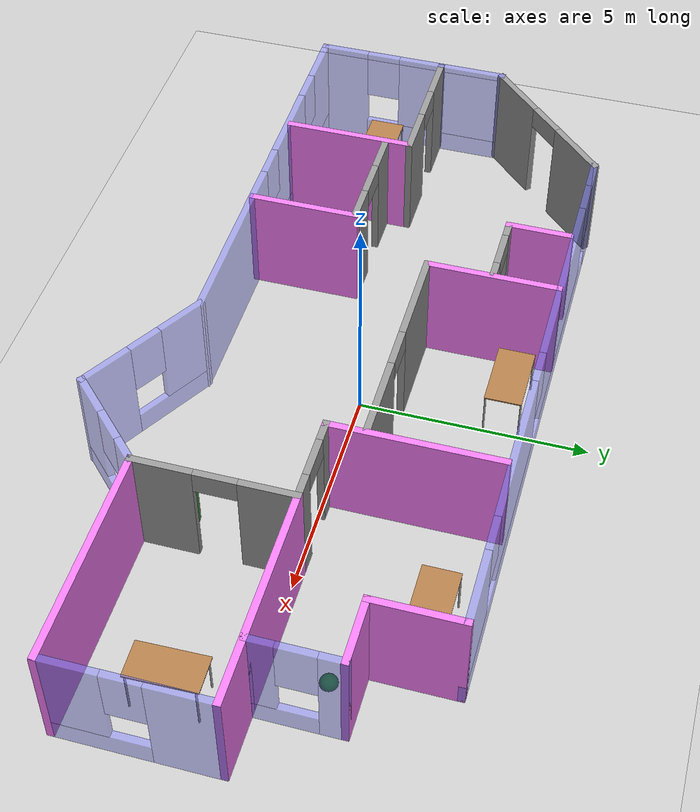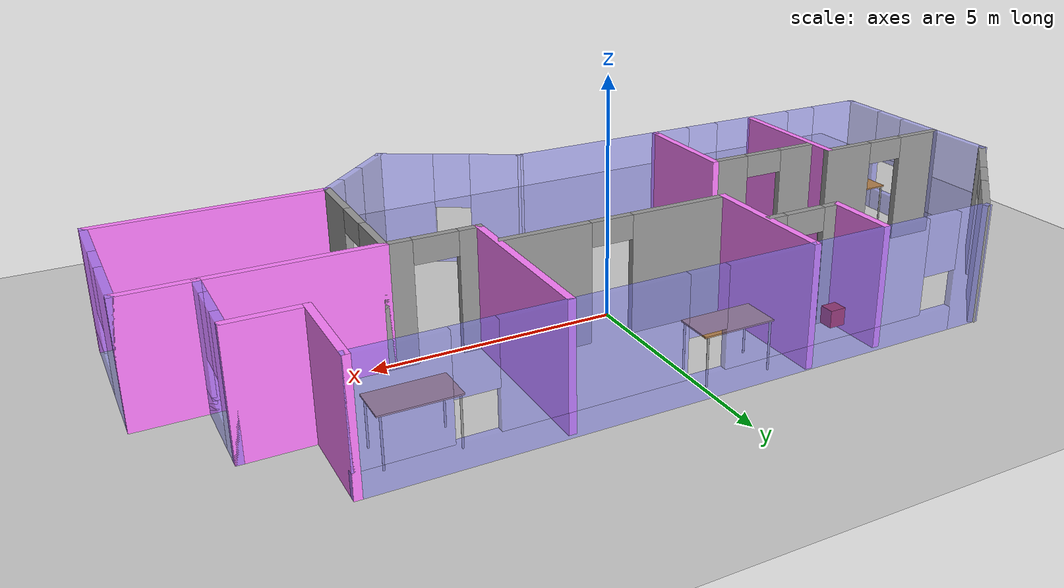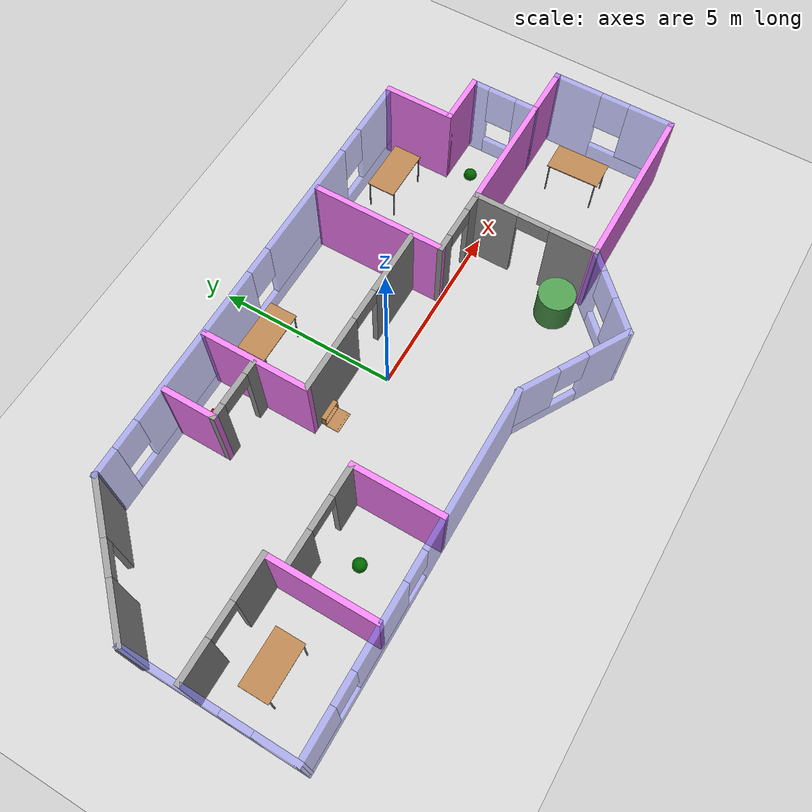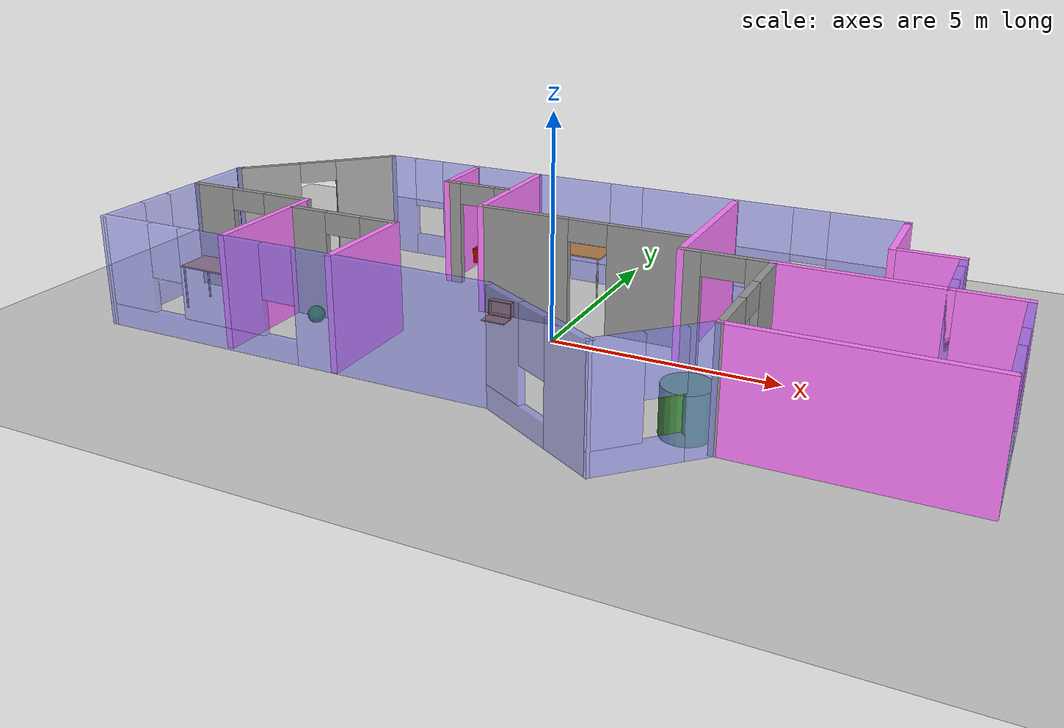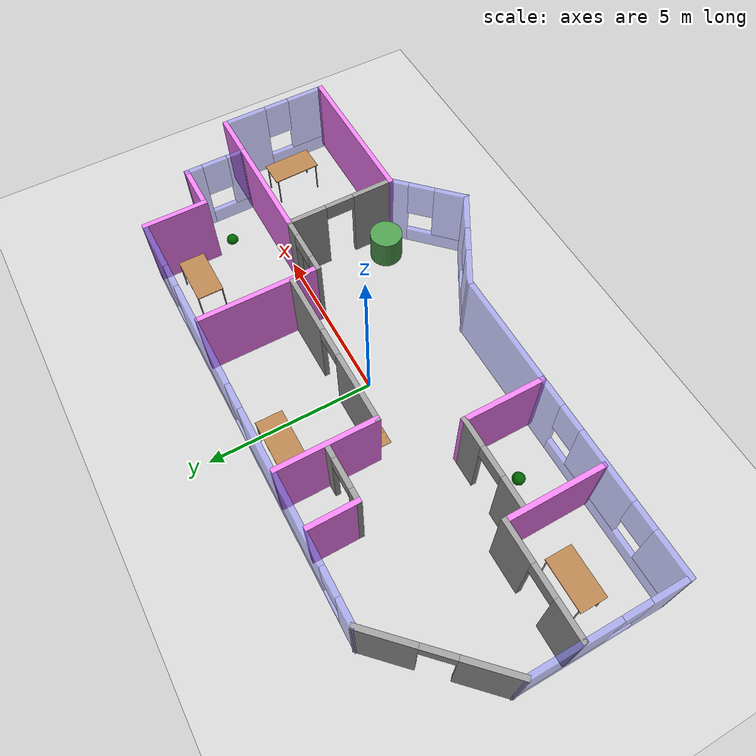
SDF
<sdf version="1.6">
 <world name="default">
  <light name="sun" type="directional">
   <pose>0 0 10 0 -0 0</pose>
   <diffuse>0.8 0.8 0.8 1</diffuse>
   <specular>0.2 0.2 0.2 1</specular>
   <attenuation>
    <range>1000</range>
    <constant>0.9</constant>
    <linear>0.01</linear>
    <quadratic>0.001</quadratic>
   </attenuation>
   <direction>-0.5 0.1 -0.9</direction>
  </light>
  <model name="ground_plane">
   <static>1</static>
   <link name="link">
    <collision name="collision">
     <geometry><plane><normal>0 0 1</normal><size>100 100</size></plane></geometry>
     <surface>
      <contact><collide_bitmask>65535</collide_bitmask></contact>
      <friction><ode><mu>100</mu><mu2>50</mu2></ode></friction>
     </surface>
    </collision>
    <visual name="visual">
     <cast_shadows>0</cast_shadows>
     <geometry><plane><normal>0 0 1</normal><size>100 100</size></plane></geometry>
     <material>
      <script><uri>file://media/materials/scripts/gazebo.material</uri><name>Gazebo/Grey</name></script>
     </material>
    </visual>
   </link>
  </model>
  <gravity>0 0 -9.8</gravity>
  <magnetic_field>6e-06 2.3e-05 -4.2e-05</magnetic_field>
  <atmosphere type="adiabatic"/>
  <physics name="default_physics" default="0" type="ode">
   <max_step_size>0.001</max_step_size>
   <real_time_factor>1</real_time_factor>
   <real_time_update_rate>1000</real_time_update_rate>
  </physics>
  <scene><ambient>0.4 0.4 0.4 1</ambient><background>0.7 0.7 0.7 1</background><shadows>1</shadows></scene>
  <spherical_coordinates>
   <surface_model>EARTH_WGS84</surface_model>
   <latitude_deg>0</latitude_deg>
   <longitude_deg>0</longitude_deg>
   <elevation>0</elevation>
   <heading_deg>0</heading_deg>
  </spherical_coordinates>
  <model name="table">
   <static>1</static>
   <link name="link">
    <collision name="surface">
     <pose>0 0 1 0 -0 0</pose>
     <geometry><box><size>1.5 0.8 0.03</size></box></geometry>
     <surface><friction><ode><mu>0.6</mu><mu2>0.6</mu2></ode></friction></surface>
    </collision>
    <visual name="visual1">
     <pose>0 0 1 0 -0 0</pose>
     <geometry><box><size>1.5 0.8 0.03</size></box></geometry>
     <material>
      <script><uri>file://media/materials/scripts/gazebo.material</uri><name>Gazebo/Wood</name></script>
     </material>
    </visual>
    <collision name="front_left_leg">
     <pose>0.68 0.38 0.5 0 -0 0</pose>
     <geometry><cylinder><radius>0.02</radius><length>1</length></cylinder></geometry>
    </collision>
    <visual name="front_left_leg">
     <pose>0.68 0.38 0.5 0 -0 0</pose>
     <geometry><cylinder><radius>0.02</radius><length>1</length></cylinder></geometry>
     <material>
      <script><uri>file://media/materials/scripts/gazebo.material</uri><name>Gazebo/Grey</name></script>
     </material>
    </visual>
    <collision name="front_right_leg">
     <pose>0.68 -0.38 0.5 0 -0 0</pose>
     <geometry><cylinder><radius>0.02</radius><length>1</length></cylinder></geometry>
    </collision>
    <visual name="front_right_leg">
     <pose>0.68 -0.38 0.5 0 -0 0</pose>
     <geometry><cylinder><radius>0.02</radius><length>1</length></cylinder></geometry>
     <material>
      <script><uri>file://media/materials/scripts/gazebo.material</uri><name>Gazebo/Grey</name></script>
     </material>
    </visual>
    <collision name="back_right_leg">
     <pose>-0.68 -0.38 0.5 0 -0 0</pose>
     <geometry><cylinder><radius>0.02</radius><length>1</length></cylinder></geometry>
    </collision>
    <visual name="back_right_leg">
     <pose>-0.68 -0.38 0.5 0 -0 0</pose>
     <geometry><cylinder><radius>0.02</radius><length>1</length></cylinder></geometry>
     <material>
      <script><uri>file://media/materials/scripts/gazebo.material</uri><name>Gazebo/Grey</name></script>
     </material>
    </visual>
    <collision name="back_left_leg">
     <pose>-0.68 0.38 0.5 0 -0 0</pose>
     <geometry><cylinder><radius>0.02</radius><length>1</length></cylinder></geometry>
    </collision>
    <visual name="back_left_leg">
     <pose>-0.68 0.38 0.5 0 -0 0</pose>
     <geometry><cylinder><radius>0.02</radius><length>1</length></cylinder></geometry>
     <material>
      <script><uri>file://media/materials/scripts/gazebo.material</uri><name>Gazebo/Grey</name></script>
     </material>
    </visual>
   </link>
   <pose>5.23184 2.86923 0 0 -0 0</pose>
  </model>
  <model name="table_0">
   <static>1</static>
   <link name="link">
    <collision name="surface">
     <pose>0 0 1 0 -0 0</pose>
     <geometry><box><size>1.5 0.8 0.03</size></box></geometry>
     <surface><friction><ode><mu>0.6</mu><mu2>0.6</mu2></ode></friction></surface>
    </collision>
    <visual name="visual1">
     <pose>0 0 1 0 -0 0</pose>
     <geometry><box><size>1.5 0.8 0.03</size></box></geometry>
     <material>
      <script><uri>file://media/materials/scripts/gazebo.material</uri><name>Gazebo/Wood</name></script>
     </material>
    </visual>
    <collision name="front_left_leg">
     <pose>0.68 0.38 0.5 0 -0 0</pose>
     <geometry><cylinder><radius>0.02</radius><length>1</length></cylinder></geometry>
    </collision>
    <visual name="front_left_leg">
     <pose>0.68 0.38 0.5 0 -0 0</pose>
     <geometry><cylinder><radius>0.02</radius><length>1</length></cylinder></geometry>
     <material>
      <script><uri>file://media/materials/scripts/gazebo.material</uri><name>Gazebo/Grey</name></script>
     </material>
    </visual>
    <collision name="front_right_leg">
     <pose>0.68 -0.38 0.5 0 -0 0</pose>
     <geometry><cylinder><radius>0.02</radius><length>1</length></cylinder></geometry>
    </collision>
    <visual name="front_right_leg">
     <pose>0.68 -0.38 0.5 0 -0 0</pose>
     <geometry><cylinder><radius>0.02</radius><length>1</length></cylinder></geometry>
     <material>
      <script><uri>file://media/materials/scripts/gazebo.material</uri><name>Gazebo/Grey</name></script>
     </material>
    </visual>
    <collision name="back_right_leg">
     <pose>-0.68 -0.38 0.5 0 -0 0</pose>
     <geometry><cylinder><radius>0.02</radius><length>1</length></cylinder></geometry>
    </collision>
    <visual name="back_right_leg">
     <pose>-0.68 -0.38 0.5 0 -0 0</pose>
     <geometry><cylinder><radius>0.02</radius><length>1</length></cylinder></geometry>
     <material>
      <script><uri>file://media/materials/scripts/gazebo.material</uri><name>Gazebo/Grey</name></script>
     </material>
    </visual>
    <collision name="back_left_leg">
     <pose>-0.68 0.38 0.5 0 -0 0</pose>
     <geometry><cylinder><radius>0.02</radius><length>1</length></cylinder></geometry>
    </collision>
    <visual name="back_left_leg">
     <pose>-0.68 0.38 0.5 0 -0 0</pose>
     <geometry><cylinder><radius>0.02</radius><length>1</length></cylinder></geometry>
     <material>
      <script><uri>file://media/materials/scripts/gazebo.material</uri><name>Gazebo/Grey</name></script>
     </material>
    </visual>
   </link>
   <pose>-0.778991 3.08278 0 0 -0 0</pose>
  </model>
  <model name="table_1">
   <static>1</static>
   <link name="link">
    <collision name="surface">
     <pose>0 0 1 0 -0 0</pose>
     <geometry><box><size>1.5 0.8 0.03</size></box></geometry>
     <surface><friction><ode><mu>0.6</mu><mu2>0.6</mu2></ode></friction></surface>
    </collision>
    <visual name="visual1">
     <pose>0 0 1 0 -0 0</pose>
     <geometry><box><size>1.5 0.8 0.03</size></box></geometry>
     <material>
      <script><uri>file://media/materials/scripts/gazebo.material</uri><name>Gazebo/Wood</name></script>
     </material>
    </visual>
    <collision name="front_left_leg">
     <pose>0.68 0.38 0.5 0 -0 0</pose>
     <geometry><cylinder><radius>0.02</radius><length>1</length></cylinder></geometry>
    </collision>
    <visual name="front_left_leg">
     <pose>0.68 0.38 0.5 0 -0 0</pose>
     <geometry><cylinder><radius>0.02</radius><length>1</length></cylinder></geometry>
     <material>
      <script><uri>file://media/materials/scripts/gazebo.material</uri><name>Gazebo/Grey</name></script>
     </material>
    </visual>
    <collision name="front_right_leg">
     <pose>0.68 -0.38 0.5 0 -0 0</pose>
     <geometry><cylinder><radius>0.02</radius><length>1</length></cylinder></geometry>
    </collision>
    <visual name="front_right_leg">
     <pose>0.68 -0.38 0.5 0 -0 0</pose>
     <geometry><cylinder><radius>0.02</radius><length>1</length></cylinder></geometry>
     <material>
      <script><uri>file://media/materials/scripts/gazebo.material</uri><name>Gazebo/Grey</name></script>
     </material>
    </visual>
    <collision name="back_right_leg">
     <pose>-0.68 -0.38 0.5 0 -0 0</pose>
     <geometry><cylinder><radius>0.02</radius><length>1</length></cylinder></geometry>
    </collision>
    <visual name="back_right_leg">
     <pose>-0.68 -0.38 0.5 0 -0 0</pose>
     <geometry><cylinder><radius>0.02</radius><length>1</length></cylinder></geometry>
     <material>
      <script><uri>file://media/materials/scripts/gazebo.material</uri><name>Gazebo/Grey</name></script>
     </material>
    </visual>
    <collision name="back_left_leg">
     <pose>-0.68 0.38 0.5 0 -0 0</pose>
     <geometry><cylinder><radius>0.02</radius><length>1</length></cylinder></geometry>
    </collision>
    <visual name="back_left_leg">
     <pose>-0.68 0.38 0.5 0 -0 0</pose>
     <geometry><cylinder><radius>0.02</radius><length>1</length></cylinder></geometry>
     <material>
      <script><uri>file://media/materials/scripts/gazebo.material</uri><name>Gazebo/Grey</name></script>
     </material>
    </visual>
   </link>
   <pose>7.93641 -1.44569 0 0 0 -1.54576</pose>
  </model>
  <plugin name="collision_map_creator" filename="libcollision_map_creator.so"/>
  <model name="wooden_case">
   <link name="base">
    <pose>0 0 0.024 0 -0 0</pose>
    <inertial>
     <pose>-0.022184 0 0.171592 0 -0 0</pose>
     <mass>3.96264</mass>
     <inertia>
      <ixx>0.213536</ixx>
      <ixy>0</ixy>
      <ixz>0.000779377</ixz>
      <iyy>0.0708943</iyy>
      <iyz>0</iyz>
      <izz>0.154604</izz>
     </inertia>
    </inertial>
    <collision name="collision_back">
     <pose>-0.053975 0 0.1778 0 -0 0</pose>
     <geometry><box><size>0.01905 0.5461 0.3175</size></box></geometry>
     <surface>
      <contact>
       <poissons_ratio>0.347</poissons_ratio>
       <elastic_modulus>8.8e+09</elastic_modulus>
       <ode><kp>100000</kp><kd>100</kd><max_vel>100</max_vel><min_depth>0.001</min_depth></ode>
      </contact>
      <friction>
       <torsional>
        <coefficient>1</coefficient>
        <use_patch_radius>0</use_patch_radius>
        <surface_radius>0.01</surface_radius>
       </torsional>
      </friction>
     </surface>
    </collision>
    <visual name="visual_back">
     <pose>-0.053975 0 0.1778 0 -0 0</pose>
     <geometry><box><size>0.01905 0.5461 0.3175</size></box></geometry>
     <material>
      <script><uri>file://media/materials/scripts/gazebo.material</uri><name>Gazebo/Wood</name></script>
     </material>
    </visual>
    <collision name="collision_bottom">
     <pose>0 0 0.009525 0 -0 0</pose>
     <geometry><box><size>0.127 0.5842 0.01905</size></box></geometry>
     <surface>
      <contact>
       <poissons_ratio>0.347</poissons_ratio>
       <elastic_modulus>8.8e+09</elastic_modulus>
       <ode><kp>100000</kp><kd>100</kd><max_vel>100</max_vel><min_depth>0.001</min_depth></ode>
      </contact>
      <friction>
       <torsional>
        <coefficient>1</coefficient>
        <use_patch_radius>0</use_patch_radius>
        <surface_radius>0.01</surface_radius>
       </torsional>
      </friction>
     </surface>
    </collision>
    <visual name="visual_bottom">
     <pose>0 0 0.009525 0 -0 0</pose>
     <geometry><box><size>0.127 0.5842 0.01905</size></box></geometry>
     <material>
      <script><uri>file://media/materials/scripts/gazebo.material</uri><name>Gazebo/Wood</name></script>
     </material>
    </visual>
    <collision name="collision_top">
     <pose>0 0 0.346075 0 -0 0</pose>
     <geometry><box><size>0.127 0.5842 0.01905</size></box></geometry>
     <surface>
      <contact>
       <poissons_ratio>0.347</poissons_ratio>
       <elastic_modulus>8.8e+09</elastic_modulus>
       <ode><kp>100000</kp><kd>100</kd><max_vel>100</max_vel><min_depth>0.001</min_depth></ode>
      </contact>
      <friction>
       <torsional>
        <coefficient>1</coefficient>
        <use_patch_radius>0</use_patch_radius>
        <surface_radius>0.01</surface_radius>
       </torsional>
      </friction>
     </surface>
    </collision>
    <visual name="visual_top">
     <pose>0 0 0.346075 0 -0 0</pose>
     <geometry><box><size>0.127 0.5842 0.01905</size></box></geometry>
     <material>
      <script><uri>file://media/materials/scripts/gazebo.material</uri><name>Gazebo/Wood</name></script>
     </material>
    </visual>
    <collision name="collision_left">
     <pose>0 -0.282575 0.1778 0 -0 0</pose>
     <geometry><box><size>0.127 0.01905 0.3175</size></box></geometry>
     <surface>
      <contact>
       <poissons_ratio>0.347</poissons_ratio>
       <elastic_modulus>8.8e+09</elastic_modulus>
       <ode><kp>100000</kp><kd>100</kd><max_vel>100</max_vel><min_depth>0.001</min_depth></ode>
      </contact>
      <friction>
       <torsional>
        <coefficient>1</coefficient>
        <use_patch_radius>0</use_patch_radius>
        <surface_radius>0.01</surface_radius>
       </torsional>
      </friction>
     </surface>
    </collision>
    <visual name="visual_left">
     <pose>0 -0.282575 0.1778 0 -0 0</pose>
     <geometry><box><size>0.127 0.01905 0.3175</size></box></geometry>
     <material>
      <script><uri>file://media/materials/scripts/gazebo.material</uri><name>Gazebo/Wood</name></script>
     </material>
    </visual>
    <collision name="collision_right">
     <pose>0 0.282575 0.1778 0 -0 0</pose>
     <geometry><box><size>0.127 0.01905 0.3175</size></box></geometry>
     <surface>
      <contact>
       <poissons_ratio>0.347</poissons_ratio>
       <elastic_modulus>8.8e+09</elastic_modulus>
       <ode><kp>100000</kp><kd>100</kd><max_vel>100</max_vel><min_depth>0.001</min_depth></ode>
      </contact>
      <friction>
       <torsional>
        <coefficient>1</coefficient>
        <use_patch_radius>0</use_patch_radius>
        <surface_radius>0.01</surface_radius>
       </torsional>
      </friction>
     </surface>
    </collision>
    <visual name="visual_right">
     <pose>0 0.282575 0.1778 0 -0 0</pose>
     <geometry><box><size>0.127 0.01905 0.3175</size></box></geometry>
     <material>
      <script><uri>file://media/materials/scripts/gazebo.material</uri><name>Gazebo/Wood</name></script>
     </material>
    </visual>
    <collision name="collision_block_left">
     <pose>0.0095 -0.2151 -0.012 0 -0 0</pose>
     <geometry><box><size>0.108 0.05 0.024</size></box></geometry>
     <surface>
      <contact>
       <poissons_ratio>0.347</poissons_ratio>
       <elastic_modulus>8.8e+09</elastic_modulus>
       <ode><kp>100000</kp><kd>100</kd><max_vel>100</max_vel><min_depth>0.001</min_depth></ode>
      </contact>
      <friction>
       <torsional>
        <coefficient>1</coefficient>
        <use_patch_radius>0</use_patch_radius>
        <surface_radius>0.01</surface_radius>
       </torsional>
      </friction>
     </surface>
    </collision>
    <visual name="visual_block_left">
     <pose>0.0095 -0.2151 -0.012 0 -0 0</pose>
     <geometry><box><size>0.108 0.05 0.024</size></box></geometry>
     <material>
      <script><uri>file://media/materials/scripts/gazebo.material</uri><name>Gazebo/Wood</name></script>
     </material>
    </visual>
    <collision name="collision_block_right">
     <pose>0.0095 0.2151 -0.012 0 -0 0</pose>
     <geometry><box><size>0.108 0.05 0.024</size></box></geometry>
     <surface>
      <contact>
       <poissons_ratio>0.347</poissons_ratio>
       <elastic_modulus>8.8e+09</elastic_modulus>
       <ode><kp>100000</kp><kd>100</kd><max_vel>100</max_vel><min_depth>0.001</min_depth></ode>
      </contact>
      <friction>
       <torsional>
        <coefficient>1</coefficient>
        <use_patch_radius>0</use_patch_radius>
        <surface_radius>0.01</surface_radius>
       </torsional>
      </friction>
     </surface>
    </collision>
    <visual name="visual_block_right">
     <pose>0.0095 0.2151 -0.012 0 -0 0</pose>
     <geometry><box><size>0.108 0.05 0.024</size></box></geometry>
     <material>
      <script><uri>file://media/materials/scripts/gazebo.material</uri><name>Gazebo/Wood</name></script>
     </material>
    </visual>
   </link>
   <link name="lid">
    <pose>0.243775 0 0.009525 0 -0 0</pose>
    <inertial>
     <mass>1.97874</mass>
     <inertia>
      <ixx>0.0563367</ixx>
      <ixy>0</ixy>
      <ixz>0</ixz>
      <iyy>0.020911</iyy>
      <iyz>0</iyz>
      <izz>0.0771281</izz>
     </inertia>
    </inertial>
    <collision name="collision">
     <geometry><box><size>0.3556 0.5842 0.01905</size></box></geometry>
     <surface>
      <contact>
       <poissons_ratio>0.347</poissons_ratio>
       <elastic_modulus>8.8e+09</elastic_modulus>
       <ode><kp>100000</kp><kd>100</kd><max_vel>100</max_vel><min_depth>0.001</min_depth></ode>
      </contact>
      <friction>
       <torsional>
        <coefficient>1</coefficient>
        <use_patch_radius>0</use_patch_radius>
        <surface_radius>0.01</surface_radius>
       </torsional>
      </friction>
     </surface>
    </collision>
    <visual name="visual">
     <geometry><box><size>0.3556 0.5842 0.01905</size></box></geometry>
     <material>
      <script><uri>file://media/materials/scripts/gazebo.material</uri><name>Gazebo/Wood</name></script>
     </material>
    </visual>
    <visual name="tee_nut_1">
     <pose>0.122 -0.216 0 0 -0 0</pose>
     <geometry><cylinder><radius>0.00635</radius><length>0.0192405</length></cylinder></geometry>
     <material>
      <script><uri>file://media/materials/scripts/gazebo.material</uri><name>Gazebo/Grey</name></script>
     </material>
    </visual>
    <visual name="tee_nut_2">
     <pose>0.122 -0.088 0 0 -0 0</pose>
     <geometry><cylinder><radius>0.00635</radius><length>0.0192405</length></cylinder></geometry>
     <material>
      <script><uri>file://media/materials/scripts/gazebo.material</uri><name>Gazebo/Grey</name></script>
     </material>
    </visual>
    <visual name="tee_nut_3">
     <pose>0.122 0.088 0 0 -0 0</pose>
     <geometry><cylinder><radius>0.00635</radius><length>0.0192405</length></cylinder></geometry>
     <material>
      <script><uri>file://media/materials/scripts/gazebo.material</uri><name>Gazebo/Grey</name></script>
     </material>
    </visual>
    <visual name="tee_nut_4">
     <pose>0.122 0.216 0 0 -0 0</pose>
     <geometry><cylinder><radius>0.00635</radius><length>0.0192405</length></cylinder></geometry>
     <material>
      <script><uri>file://media/materials/scripts/gazebo.material</uri><name>Gazebo/Grey</name></script>
     </material>
    </visual>
   </link>
   <joint name="lid_hinge" type="revolute">
    <pose>-0.1778 0 0.01905 0 -0 0</pose>
    <parent>base</parent>
    <child>lid</child>
    <axis>
     <xyz>0 1 0</xyz>
     <limit><upper>0.523599</upper><lower>-1.5708</lower></limit>
     <use_parent_model_frame>0</use_parent_model_frame>
     <dynamics><spring_reference>0</spring_reference><spring_stiffness>0</spring_stiffness></dynamics>
    </axis>
   </joint>
   <pose>-1.61048 0.741559 -0.001057 0 -0.000429 -1.56956</pose>
  </model>
  <model name="table_2">
   <static>1</static>
   <link name="link">
    <collision name="surface">
     <pose>0 0 1 0 -0 0</pose>
     <geometry><box><size>1.5 0.8 0.03</size></box></geometry>
     <surface><friction><ode><mu>0.6</mu><mu2>0.6</mu2></ode></friction></surface>
    </collision>
    <visual name="visual1">
     <pose>0 0 1 0 -0 0</pose>
     <geometry><box><size>1.5 0.8 0.03</size></box></geometry>
     <material>
      <script><uri>file://media/materials/scripts/gazebo.material</uri><name>Gazebo/Wood</name></script>
     </material>
    </visual>
    <collision name="front_left_leg">
     <pose>0.68 0.38 0.5 0 -0 0</pose>
     <geometry><cylinder><radius>0.02</radius><length>1</length></cylinder></geometry>
    </collision>
    <visual name="front_left_leg">
     <pose>0.68 0.38 0.5 0 -0 0</pose>
     <geometry><cylinder><radius>0.02</radius><length>1</length></cylinder></geometry>
     <material>
      <script><uri>file://media/materials/scripts/gazebo.material</uri><name>Gazebo/Grey</name></script>
     </material>
    </visual>
    <collision name="front_right_leg">
     <pose>0.68 -0.38 0.5 0 -0 0</pose>
     <geometry><cylinder><radius>0.02</radius><length>1</length></cylinder></geometry>
    </collision>
    <visual name="front_right_leg">
     <pose>0.68 -0.38 0.5 0 -0 0</pose>
     <geometry><cylinder><radius>0.02</radius><length>1</length></cylinder></geometry>
     <material>
      <script><uri>file://media/materials/scripts/gazebo.material</uri><name>Gazebo/Grey</name></script>
     </material>
    </visual>
    <collision name="back_right_leg">
     <pose>-0.68 -0.38 0.5 0 -0 0</pose>
     <geometry><cylinder><radius>0.02</radius><length>1</length></cylinder></geometry>
    </collision>
    <visual name="back_right_leg">
     <pose>-0.68 -0.38 0.5 0 -0 0</pose>
     <geometry><cylinder><radius>0.02</radius><length>1</length></cylinder></geometry>
     <material>
      <script><uri>file://media/materials/scripts/gazebo.material</uri><name>Gazebo/Grey</name></script>
     </material>
    </visual>
    <collision name="back_left_leg">
     <pose>-0.68 0.38 0.5 0 -0 0</pose>
     <geometry><cylinder><radius>0.02</radius><length>1</length></cylinder></geometry>
    </collision>
    <visual name="back_left_leg">
     <pose>-0.68 0.38 0.5 0 -0 0</pose>
     <geometry><cylinder><radius>0.02</radius><length>1</length></cylinder></geometry>
     <material>
      <script><uri>file://media/materials/scripts/gazebo.material</uri><name>Gazebo/Grey</name></script>
     </material>
    </visual>
   </link>
   <pose>-7.62979 -1.60292 0 0 -0 0</pose>
  </model>
  <model name="house">
   <link name="Wall_10">
    <pose>3.72086 -3.525 0 0 0 -2.35619</pose>
    <inertial>
     <mass>1</mass>
     <inertia><ixx>1</ixx><ixy>0</ixy><ixz>0</ixz><iyy>1</iyy><iyz>0</iyz><izz>1</izz></inertia>
    </inertial>
    <visual name="Wall_10_Visual_0">
     <pose>-0.917996 0 1.25 0 -0 0</pose>
     <geometry><box><size>0.664008 0.15 2.5</size></box></geometry>
     <material>
      <script><uri>file://media/materials/scripts/gazebo.material</uri><name>Gazebo/Grey</name></script>
      <ambient>0.5 0.5 1 0.5</ambient>
      <shader type="pixel"><normal_map>__default__</normal_map></shader>
      <diffuse>0.7 0.7 0.7 1</diffuse>
      <specular>0.01 0.01 0.01 1</specular>
      <emissive>0 0 0 1</emissive>
     </material>
     <meta><layer>0</layer></meta>
    </visual>
    <visual name="Wall_10_Visual_1">
     <pose>0.332004 0 0.25 0 -0 0</pose>
     <geometry><box><size>1.83599 0.15 0.5</size></box></geometry>
     <material>
      <script><uri>file://media/materials/scripts/gazebo.material</uri><name>Gazebo/Grey</name></script>
      <ambient>0.5 0.5 1 0.5</ambient>
      <shader type="pixel"><normal_map>__default__</normal_map></shader>
      <diffuse>0.7 0.7 0.7 1</diffuse>
      <specular>0.01 0.01 0.01 1</specular>
      <emissive>0 0 0 1</emissive>
     </material>
     <meta><layer>0</layer></meta>
    </visual>
    <visual name="Wall_10_Visual_2">
     <pose>0.732004 0 1.5 0 -0 0</pose>
     <geometry><box><size>1.03599 0.15 2</size></box></geometry>
     <material>
      <script><uri>file://media/materials/scripts/gazebo.material</uri><name>Gazebo/Grey</name></script>
      <ambient>0.5 0.5 1 0.5</ambient>
      <shader type="pixel"><normal_map>__default__</normal_map></shader>
      <diffuse>0.7 0.7 0.7 1</diffuse>
      <specular>0.01 0.01 0.01 1</specular>
      <emissive>0 0 0 1</emissive>
     </material>
     <meta><layer>0</layer></meta>
    </visual>
    <visual name="Wall_10_Visual_3">
     <pose>-0.185992 0 1.9 0 -0 0</pose>
     <geometry><box><size>0.8 0.15 1.2</size></box></geometry>
     <material>
      <script><uri>file://media/materials/scripts/gazebo.material</uri><name>Gazebo/Grey</name></script>
      <ambient>0.5 0.5 1 0.5</ambient>
      <shader type="pixel"><normal_map>__default__</normal_map></shader>
      <diffuse>0.7 0.7 0.7 1</diffuse>
      <specular>0.01 0.01 0.01 1</specular>
      <emissive>0 0 0 1</emissive>
     </material>
     <meta><layer>0</layer></meta>
    </visual>
    <collision name="Wall_10_Collision_0">
     <pose>-0.917996 0 1.25 0 -0 0</pose>
     <geometry><box><size>0.664008 0.15 2.5</size></box></geometry>
     <surface>
      <friction>
       <ode><mu>1</mu><mu2>1</mu2><fdir1>0 0 0</fdir1><slip1>0</slip1><slip2>0</slip2></ode>
       <torsional>
        <coefficient>1</coefficient>
        <patch_radius>0</patch_radius>
        <surface_radius>0</surface_radius>
        <use_patch_radius>1</use_patch_radius>
        <ode><slip>0</slip></ode>
       </torsional>
      </friction>
      <bounce><restitution_coefficient>0</restitution_coefficient><threshold>1e+06</threshold></bounce>
      <contact>
       <collide_without_contact>0</collide_without_contact>
       <collide_without_contact_bitmask>1</collide_without_contact_bitmask>
       <collide_bitmask>1</collide_bitmask>
       <ode>
        <soft_cfm>0</soft_cfm>
        <soft_erp>0.2</soft_erp>
        <kp>1e+13</kp>
        <kd>1</kd>
        <max_vel>0.01</max_vel>
        <min_depth>0</min_depth>
       </ode>
       <bullet>
        <split_impulse>1</split_impulse>
        <split_impulse_penetration_threshold>-0.01</split_impulse_penetration_threshold>
        <soft_cfm>0</soft_cfm>
        <soft_erp>0.2</soft_erp>
        <kp>1e+13</kp>
        <kd>1</kd>
       </bullet>
      </contact>
     </surface>
    </collision>
    <collision name="Wall_10_Collision_1">
     <pose>0.332004 0 0.25 0 -0 0</pose>
     <geometry><box><size>1.83599 0.15 0.5</size></box></geometry>
     <surface>
      <friction>
       <ode><mu>1</mu><mu2>1</mu2><fdir1>0 0 0</fdir1><slip1>0</slip1><slip2>0</slip2></ode>
       <torsional>
        <coefficient>1</coefficient>
        <patch_radius>0</patch_radius>
        <surface_radius>0</surface_radius>
        <use_patch_radius>1</use_patch_radius>
        <ode><slip>0</slip></ode>
       </torsional>
      </friction>
      <bounce><restitution_coefficient>0</restitution_coefficient><threshold>1e+06</threshold></bounce>
      <contact>
       <collide_without_contact>0</collide_without_contact>
       <collide_without_contact_bitmask>1</collide_without_contact_bitmask>
       <collide_bitmask>1</collide_bitmask>
       <ode>
        <soft_cfm>0</soft_cfm>
        <soft_erp>0.2</soft_erp>
        <kp>1e+13</kp>
        <kd>1</kd>
        <max_vel>0.01</max_vel>
        <min_depth>0</min_depth>
       </ode>
       <bullet>
        <split_impulse>1</split_impulse>
        <split_impulse_penetration_threshold>-0.01</split_impulse_penetration_threshold>
        <soft_cfm>0</soft_cfm>
        <soft_erp>0.2</soft_erp>
        <kp>1e+13</kp>
        <kd>1</kd>
       </bullet>
      </contact>
     </surface>
    </collision>
    <collision name="Wall_10_Collision_2">
     <pose>0.732004 0 1.5 0 -0 0</pose>
     <geometry><box><size>1.03599 0.15 2</size></box></geometry>
     <surface>
      <friction>
       <ode><mu>1</mu><mu2>1</mu2><fdir1>0 0 0</fdir1><slip1>0</slip1><slip2>0</slip2></ode>
       <torsional>
        <coefficient>1</coefficient>
        <patch_radius>0</patch_radius>
        <surface_radius>0</surface_radius>
        <use_patch_radius>1</use_patch_radius>
        <ode><slip>0</slip></ode>
       </torsional>
      </friction>
      <bounce><restitution_coefficient>0</restitution_coefficient><threshold>1e+06</threshold></bounce>
      <contact>
       <collide_without_contact>0</collide_without_contact>
       <collide_without_contact_bitmask>1</collide_without_contact_bitmask>
       <collide_bitmask>1</collide_bitmask>
       <ode>
        <soft_cfm>0</soft_cfm>
        <soft_erp>0.2</soft_erp>
        <kp>1e+13</kp>
        <kd>1</kd>
        <max_vel>0.01</max_vel>
        <min_depth>0</min_depth>
       </ode>
       <bullet>
        <split_impulse>1</split_impulse>
        <split_impulse_penetration_threshold>-0.01</split_impulse_penetration_threshold>
        <soft_cfm>0</soft_cfm>
        <soft_erp>0.2</soft_erp>
        <kp>1e+13</kp>
        <kd>1</kd>
       </bullet>
      </contact>
     </surface>
    </collision>
    <collision name="Wall_10_Collision_3">
     <pose>-0.185992 0 1.9 0 -0 0</pose>
     <geometry><box><size>0.8 0.15 1.2</size></box></geometry>
     <surface>
      <friction>
       <ode><mu>1</mu><mu2>1</mu2><fdir1>0 0 0</fdir1><slip1>0</slip1><slip2>0</slip2></ode>
       <torsional>
        <coefficient>1</coefficient>
        <patch_radius>0</patch_radius>
        <surface_radius>0</surface_radius>
        <use_patch_radius>1</use_patch_radius>
        <ode><slip>0</slip></ode>
       </torsional>
      </friction>
      <bounce><restitution_coefficient>0</restitution_coefficient><threshold>1e+06</threshold></bounce>
      <contact>
       <collide_without_contact>0</collide_without_contact>
       <collide_without_contact_bitmask>1</collide_without_contact_bitmask>
       <collide_bitmask>1</collide_bitmask>
       <ode>
        <soft_cfm>0</soft_cfm>
        <soft_erp>0.2</soft_erp>
        <kp>1e+13</kp>
        <kd>1</kd>
        <max_vel>0.01</max_vel>
        <min_depth>0</min_depth>
       </ode>
       <bullet>
        <split_impulse>1</split_impulse>
        <split_impulse_penetration_threshold>-0.01</split_impulse_penetration_threshold>
        <soft_cfm>0</soft_cfm>
        <soft_erp>0.2</soft_erp>
        <kp>1e+13</kp>
        <kd>1</kd>
       </bullet>
      </contact>
     </surface>
    </collision>
   </link>
   <link name="Wall_11">
    <pose>1.54767 -3.58085 0 0 -0 2.61799</pose>
    <inertial>
     <mass>1</mass>
     <inertia><ixx>1</ixx><ixy>0</ixy><ixz>0</ixz><iyy>1</iyy><iyz>0</iyz><izz>1</izz></inertia>
    </inertial>
    <visual name="Wall_11_Visual_0">
     <pose>-0.990098 0 1.25 0 -0 0</pose>
     <geometry><box><size>1.2698 0.15 2.5</size></box></geometry>
     <material>
      <script><uri>file://media/materials/scripts/gazebo.material</uri><name>Gazebo/Grey</name></script>
      <ambient>0.5 0.5 1 0.5</ambient>
      <shader type="pixel"><normal_map>__default__</normal_map></shader>
      <diffuse>0.7 0.7 0.7 1</diffuse>
      <specular>0.01 0.01 0.01 1</specular>
      <emissive>0 0 0 1</emissive>
     </material>
     <meta><layer>0</layer></meta>
    </visual>
    <visual name="Wall_11_Visual_1">
     <pose>0.634902 0 0.25 0 -0 0</pose>
     <geometry><box><size>1.9802 0.15 0.5</size></box></geometry>
     <material>
      <script><uri>file://media/materials/scripts/gazebo.material</uri><name>Gazebo/Grey</name></script>
      <ambient>0.5 0.5 1 0.5</ambient>
      <shader type="pixel"><normal_map>__default__</normal_map></shader>
      <diffuse>0.7 0.7 0.7 1</diffuse>
      <specular>0.01 0.01 0.01 1</specular>
      <emissive>0 0 0 1</emissive>
     </material>
     <meta><layer>0</layer></meta>
    </visual>
    <visual name="Wall_11_Visual_2">
     <pose>1.0349 0 1.5 0 -0 0</pose>
     <geometry><box><size>1.1802 0.15 2</size></box></geometry>
     <material>
      <script><uri>file://media/materials/scripts/gazebo.material</uri><name>Gazebo/Grey</name></script>
      <ambient>0.5 0.5 1 0.5</ambient>
      <shader type="pixel"><normal_map>__default__</normal_map></shader>
      <diffuse>0.7 0.7 0.7 1</diffuse>
      <specular>0.01 0.01 0.01 1</specular>
      <emissive>0 0 0 1</emissive>
     </material>
     <meta><layer>0</layer></meta>
    </visual>
    <visual name="Wall_11_Visual_3">
     <pose>0.044803 0 1.9 0 -0 0</pose>
     <geometry><box><size>0.8 0.15 1.2</size></box></geometry>
     <material>
      <script><uri>file://media/materials/scripts/gazebo.material</uri><name>Gazebo/Grey</name></script>
      <ambient>0.5 0.5 1 0.5</ambient>
      <shader type="pixel"><normal_map>__default__</normal_map></shader>
      <diffuse>0.7 0.7 0.7 1</diffuse>
      <specular>0.01 0.01 0.01 1</specular>
      <emissive>0 0 0 1</emissive>
     </material>
     <meta><layer>0</layer></meta>
    </visual>
    <collision name="Wall_11_Collision_0">
     <pose>-0.990098 0 1.25 0 -0 0</pose>
     <geometry><box><size>1.2698 0.15 2.5</size></box></geometry>
     <surface>
      <friction>
       <ode><mu>1</mu><mu2>1</mu2><fdir1>0 0 0</fdir1><slip1>0</slip1><slip2>0</slip2></ode>
       <torsional>
        <coefficient>1</coefficient>
        <patch_radius>0</patch_radius>
        <surface_radius>0</surface_radius>
        <use_patch_radius>1</use_patch_radius>
        <ode><slip>0</slip></ode>
       </torsional>
      </friction>
      <bounce><restitution_coefficient>0</restitution_coefficient><threshold>1e+06</threshold></bounce>
      <contact>
       <collide_without_contact>0</collide_without_contact>
       <collide_without_contact_bitmask>1</collide_without_contact_bitmask>
       <collide_bitmask>1</collide_bitmask>
       <ode>
        <soft_cfm>0</soft_cfm>
        <soft_erp>0.2</soft_erp>
        <kp>1e+13</kp>
        <kd>1</kd>
        <max_vel>0.01</max_vel>
        <min_depth>0</min_depth>
       </ode>
       <bullet>
        <split_impulse>1</split_impulse>
        <split_impulse_penetration_threshold>-0.01</split_impulse_penetration_threshold>
        <soft_cfm>0</soft_cfm>
        <soft_erp>0.2</soft_erp>
        <kp>1e+13</kp>
        <kd>1</kd>
       </bullet>
      </contact>
     </surface>
    </collision>
    <collision name="Wall_11_Collision_1">
     <pose>0.634902 0 0.25 0 -0 0</pose>
     <geometry><box><size>1.9802 0.15 0.5</size></box></geometry>
     <surface>
      <friction>
       <ode><mu>1</mu><mu2>1</mu2><fdir1>0 0 0</fdir1><slip1>0</slip1><slip2>0</slip2></ode>
       <torsional>
        <coefficient>1</coefficient>
        <patch_radius>0</patch_radius>
        <surface_radius>0</surface_radius>
        <use_patch_radius>1</use_patch_radius>
        <ode><slip>0</slip></ode>
       </torsional>
      </friction>
      <bounce><restitution_coefficient>0</restitution_coefficient><threshold>1e+06</threshold></bounce>
      <contact>
       <collide_without_contact>0</collide_without_contact>
       <collide_without_contact_bitmask>1</collide_without_contact_bitmask>
       <collide_bitmask>1</collide_bitmask>
       <ode>
        <soft_cfm>0</soft_cfm>
        <soft_erp>0.2</soft_erp>
        <kp>1e+13</kp>
        <kd>1</kd>
        <max_vel>0.01</max_vel>
        <min_depth>0</min_depth>
       </ode>
       <bullet>
        <split_impulse>1</split_impulse>
        <split_impulse_penetration_threshold>-0.01</split_impulse_penetration_threshold>
        <soft_cfm>0</soft_cfm>
        <soft_erp>0.2</soft_erp>
        <kp>1e+13</kp>
        <kd>1</kd>
       </bullet>
      </contact>
     </surface>
    </collision>
    <collision name="Wall_11_Collision_2">
     <pose>1.0349 0 1.5 0 -0 0</pose>
     <geometry><box><size>1.1802 0.15 2</size></box></geometry>
     <surface>
      <friction>
       <ode><mu>1</mu><mu2>1</mu2><fdir1>0 0 0</fdir1><slip1>0</slip1><slip2>0</slip2></ode>
       <torsional>
        <coefficient>1</coefficient>
        <patch_radius>0</patch_radius>
        <surface_radius>0</surface_radius>
        <use_patch_radius>1</use_patch_radius>
        <ode><slip>0</slip></ode>
       </torsional>
      </friction>
      <bounce><restitution_coefficient>0</restitution_coefficient><threshold>1e+06</threshold></bounce>
      <contact>
       <collide_without_contact>0</collide_without_contact>
       <collide_without_contact_bitmask>1</collide_without_contact_bitmask>
       <collide_bitmask>1</collide_bitmask>
       <ode>
        <soft_cfm>0</soft_cfm>
        <soft_erp>0.2</soft_erp>
        <kp>1e+13</kp>
        <kd>1</kd>
        <max_vel>0.01</max_vel>
        <min_depth>0</min_depth>
       </ode>
       <bullet>
        <split_impulse>1</split_impulse>
        <split_impulse_penetration_threshold>-0.01</split_impulse_penetration_threshold>
        <soft_cfm>0</soft_cfm>
        <soft_erp>0.2</soft_erp>
        <kp>1e+13</kp>
        <kd>1</kd>
       </bullet>
      </contact>
     </surface>
    </collision>
    <collision name="Wall_11_Collision_3">
     <pose>0.044803 0 1.9 0 -0 0</pose>
     <geometry><box><size>0.8 0.15 1.2</size></box></geometry>
     <surface>
      <friction>
       <ode><mu>1</mu><mu2>1</mu2><fdir1>0 0 0</fdir1><slip1>0</slip1><slip2>0</slip2></ode>
       <torsional>
        <coefficient>1</coefficient>
        <patch_radius>0</patch_radius>
        <surface_radius>0</surface_radius>
        <use_patch_radius>1</use_patch_radius>
        <ode><slip>0</slip></ode>
       </torsional>
      </friction>
      <bounce><restitution_coefficient>0</restitution_coefficient><threshold>1e+06</threshold></bounce>
      <contact>
       <collide_without_contact>0</collide_without_contact>
       <collide_without_contact_bitmask>1</collide_without_contact_bitmask>
       <collide_bitmask>1</collide_bitmask>
       <ode>
        <soft_cfm>0</soft_cfm>
        <soft_erp>0.2</soft_erp>
        <kp>1e+13</kp>
        <kd>1</kd>
        <max_vel>0.01</max_vel>
        <min_depth>0</min_depth>
       </ode>
       <bullet>
        <split_impulse>1</split_impulse>
        <split_impulse_penetration_threshold>-0.01</split_impulse_penetration_threshold>
        <soft_cfm>0</soft_cfm>
        <soft_erp>0.2</soft_erp>
        <kp>1e+13</kp>
        <kd>1</kd>
       </bullet>
      </contact>
     </surface>
    </collision>
   </link>
   <link name="Wall_12">
    <pose>-4.46967 -2.80585 0 0 -0 3.14159</pose>
    <inertial>
     <mass>1</mass>
     <inertia><ixx>1</ixx><ixy>0</ixy><ixz>0</ixz><iyy>1</iyy><iyz>0</iyz><izz>1</izz></inertia>
    </inertial>
    <visual name="Wall_12_Visual_0">
     <pose>-2.52226 0 1.25 0 -0 0</pose>
     <geometry><box><size>4.45547 0.15 2.5</size></box></geometry>
     <material>
      <script><uri>file://media/materials/scripts/gazebo.material</uri><name>Gazebo/Grey</name></script>
      <ambient>0.5 0.5 1 0.5</ambient>
      <shader type="pixel"><normal_map>__default__</normal_map></shader>
      <diffuse>0.7 0.7 0.7 1</diffuse>
      <specular>0.01 0.01 0.01 1</specular>
      <emissive>0 0 0 1</emissive>
     </material>
     <meta><layer>0</layer></meta>
    </visual>
    <visual name="Wall_12_Visual_1">
     <pose>2.22774 0 0.25 0 -0 0</pose>
     <geometry><box><size>5.04453 0.15 0.5</size></box></geometry>
     <material>
      <script><uri>file://media/materials/scripts/gazebo.material</uri><name>Gazebo/Grey</name></script>
      <ambient>0.5 0.5 1 0.5</ambient>
      <shader type="pixel"><normal_map>__default__</normal_map></shader>
      <diffuse>0.7 0.7 0.7 1</diffuse>
      <specular>0.01 0.01 0.01 1</specular>
      <emissive>0 0 0 1</emissive>
     </material>
     <meta><layer>0</layer></meta>
    </visual>
    <visual name="Wall_12_Visual_5">
     <pose>3.01993 0 1.9 0 -0 0</pose>
     <geometry><box><size>0.8 0.15 1.2</size></box></geometry>
     <material>
      <script><uri>file://media/materials/scripts/gazebo.material</uri><name>Gazebo/Grey</name></script>
      <ambient>0.5 0.5 1 0.5</ambient>
      <shader type="pixel"><normal_map>__default__</normal_map></shader>
      <diffuse>0.7 0.7 0.7 1</diffuse>
      <specular>0.01 0.01 0.01 1</specular>
      <emissive>0 0 0 1</emissive>
     </material>
     <meta><layer>0</layer></meta>
    </visual>
    <visual name="Wall_12_Visual_2">
     <pose>1.5627 0 1.5 0 -0 0</pose>
     <geometry><box><size>2.11446 0.15 2</size></box></geometry>
     <material>
      <script><uri>file://media/materials/scripts/gazebo.material</uri><name>Gazebo/Grey</name></script>
      <ambient>0.5 0.5 1 0.5</ambient>
      <shader type="pixel"><normal_map>__default__</normal_map></shader>
      <diffuse>0.7 0.7 0.7 1</diffuse>
      <specular>0.01 0.01 0.01 1</specular>
      <emissive>0 0 0 1</emissive>
     </material>
     <meta><layer>0</layer></meta>
    </visual>
    <visual name="Wall_12_Visual_3">
     <pose>4.08496 0 1.5 0 -0 0</pose>
     <geometry><box><size>1.33007 0.15 2</size></box></geometry>
     <material>
      <script><uri>file://media/materials/scripts/gazebo.material</uri><name>Gazebo/Grey</name></script>
      <ambient>0.5 0.5 1 0.5</ambient>
      <shader type="pixel"><normal_map>__default__</normal_map></shader>
      <diffuse>0.7 0.7 0.7 1</diffuse>
      <specular>0.01 0.01 0.01 1</specular>
      <emissive>0 0 0 1</emissive>
     </material>
     <meta><layer>0</layer></meta>
    </visual>
    <visual name="Wall_12_Visual_4">
     <pose>0.10547 0 1.9 0 -0 0</pose>
     <geometry><box><size>0.8 0.15 1.2</size></box></geometry>
     <material>
      <script><uri>file://media/materials/scripts/gazebo.material</uri><name>Gazebo/Grey</name></script>
      <ambient>0.5 0.5 1 0.5</ambient>
      <shader type="pixel"><normal_map>__default__</normal_map></shader>
      <diffuse>0.7 0.7 0.7 1</diffuse>
      <specular>0.01 0.01 0.01 1</specular>
      <emissive>0 0 0 1</emissive>
     </material>
     <meta><layer>0</layer></meta>
    </visual>
    <collision name="Wall_12_Collision_0">
     <pose>-2.52226 0 1.25 0 -0 0</pose>
     <geometry><box><size>4.45547 0.15 2.5</size></box></geometry>
     <surface>
      <friction>
       <ode><mu>1</mu><mu2>1</mu2><fdir1>0 0 0</fdir1><slip1>0</slip1><slip2>0</slip2></ode>
       <torsional>
        <coefficient>1</coefficient>
        <patch_radius>0</patch_radius>
        <surface_radius>0</surface_radius>
        <use_patch_radius>1</use_patch_radius>
        <ode><slip>0</slip></ode>
       </torsional>
      </friction>
      <bounce><restitution_coefficient>0</restitution_coefficient><threshold>1e+06</threshold></bounce>
      <contact>
       <collide_without_contact>0</collide_without_contact>
       <collide_without_contact_bitmask>1</collide_without_contact_bitmask>
       <collide_bitmask>1</collide_bitmask>
       <ode>
        <soft_cfm>0</soft_cfm>
        <soft_erp>0.2</soft_erp>
        <kp>1e+13</kp>
        <kd>1</kd>
        <max_vel>0.01</max_vel>
        <min_depth>0</min_depth>
       </ode>
       <bullet>
        <split_impulse>1</split_impulse>
        <split_impulse_penetration_threshold>-0.01</split_impulse_penetration_threshold>
        <soft_cfm>0</soft_cfm>
        <soft_erp>0.2</soft_erp>
        <kp>1e+13</kp>
        <kd>1</kd>
       </bullet>
      </contact>
     </surface>
    </collision>
    <collision name="Wall_12_Collision_1">
     <pose>2.22774 0 0.25 0 -0 0</pose>
     <geometry><box><size>5.04453 0.15 0.5</size></box></geometry>
     <surface>
      <friction>
       <ode><mu>1</mu><mu2>1</mu2><fdir1>0 0 0</fdir1><slip1>0</slip1><slip2>0</slip2></ode>
       <torsional>
        <coefficient>1</coefficient>
        <patch_radius>0</patch_radius>
        <surface_radius>0</surface_radius>
        <use_patch_radius>1</use_patch_radius>
        <ode><slip>0</slip></ode>
       </torsional>
      </friction>
      <bounce><restitution_coefficient>0</restitution_coefficient><threshold>1e+06</threshold></bounce>
      <contact>
       <collide_without_contact>0</collide_without_contact>
       <collide_without_contact_bitmask>1</collide_without_contact_bitmask>
       <collide_bitmask>1</collide_bitmask>
       <ode>
        <soft_cfm>0</soft_cfm>
        <soft_erp>0.2</soft_erp>
        <kp>1e+13</kp>
        <kd>1</kd>
        <max_vel>0.01</max_vel>
        <min_depth>0</min_depth>
       </ode>
       <bullet>
        <split_impulse>1</split_impulse>
        <split_impulse_penetration_threshold>-0.01</split_impulse_penetration_threshold>
        <soft_cfm>0</soft_cfm>
        <soft_erp>0.2</soft_erp>
        <kp>1e+13</kp>
        <kd>1</kd>
       </bullet>
      </contact>
     </surface>
    </collision>
    <collision name="Wall_12_Collision_5">
     <pose>3.01993 0 1.9 0 -0 0</pose>
     <geometry><box><size>0.8 0.15 1.2</size></box></geometry>
     <surface>
      <friction>
       <ode><mu>1</mu><mu2>1</mu2><fdir1>0 0 0</fdir1><slip1>0</slip1><slip2>0</slip2></ode>
       <torsional>
        <coefficient>1</coefficient>
        <patch_radius>0</patch_radius>
        <surface_radius>0</surface_radius>
        <use_patch_radius>1</use_patch_radius>
        <ode><slip>0</slip></ode>
       </torsional>
      </friction>
      <bounce><restitution_coefficient>0</restitution_coefficient><threshold>1e+06</threshold></bounce>
      <contact>
       <collide_without_contact>0</collide_without_contact>
       <collide_without_contact_bitmask>1</collide_without_contact_bitmask>
       <collide_bitmask>1</collide_bitmask>
       <ode>
        <soft_cfm>0</soft_cfm>
        <soft_erp>0.2</soft_erp>
        <kp>1e+13</kp>
        <kd>1</kd>
        <max_vel>0.01</max_vel>
        <min_depth>0</min_depth>
       </ode>
       <bullet>
        <split_impulse>1</split_impulse>
        <split_impulse_penetration_threshold>-0.01</split_impulse_penetration_threshold>
        <soft_cfm>0</soft_cfm>
        <soft_erp>0.2</soft_erp>
        <kp>1e+13</kp>
        <kd>1</kd>
       </bullet>
      </contact>
     </surface>
    </collision>
    <collision name="Wall_12_Collision_2">
     <pose>1.5627 0 1.5 0 -0 0</pose>
     <geometry><box><size>2.11446 0.15 2</size></box></geometry>
     <surface>
      <friction>
       <ode><mu>1</mu><mu2>1</mu2><fdir1>0 0 0</fdir1><slip1>0</slip1><slip2>0</slip2></ode>
       <torsional>
        <coefficient>1</coefficient>
        <patch_radius>0</patch_radius>
        <surface_radius>0</surface_radius>
        <use_patch_radius>1</use_patch_radius>
        <ode><slip>0</slip></ode>
       </torsional>
      </friction>
      <bounce><restitution_coefficient>0</restitution_coefficient><threshold>1e+06</threshold></bounce>
      <contact>
       <collide_without_contact>0</collide_without_contact>
       <collide_without_contact_bitmask>1</collide_without_contact_bitmask>
       <collide_bitmask>1</collide_bitmask>
       <ode>
        <soft_cfm>0</soft_cfm>
        <soft_erp>0.2</soft_erp>
        <kp>1e+13</kp>
        <kd>1</kd>
        <max_vel>0.01</max_vel>
        <min_depth>0</min_depth>
       </ode>
       <bullet>
        <split_impulse>1</split_impulse>
        <split_impulse_penetration_threshold>-0.01</split_impulse_penetration_threshold>
        <soft_cfm>0</soft_cfm>
        <soft_erp>0.2</soft_erp>
        <kp>1e+13</kp>
        <kd>1</kd>
       </bullet>
      </contact>
     </surface>
    </collision>
    <collision name="Wall_12_Collision_3">
     <pose>4.08496 0 1.5 0 -0 0</pose>
     <geometry><box><size>1.33007 0.15 2</size></box></geometry>
     <surface>
      <friction>
       <ode><mu>1</mu><mu2>1</mu2><fdir1>0 0 0</fdir1><slip1>0</slip1><slip2>0</slip2></ode>
       <torsional>
        <coefficient>1</coefficient>
        <patch_radius>0</patch_radius>
        <surface_radius>0</surface_radius>
        <use_patch_radius>1</use_patch_radius>
        <ode><slip>0</slip></ode>
       </torsional>
      </friction>
      <bounce><restitution_coefficient>0</restitution_coefficient><threshold>1e+06</threshold></bounce>
      <contact>
       <collide_without_contact>0</collide_without_contact>
       <collide_without_contact_bitmask>1</collide_without_contact_bitmask>
       <collide_bitmask>1</collide_bitmask>
       <ode>
        <soft_cfm>0</soft_cfm>
        <soft_erp>0.2</soft_erp>
        <kp>1e+13</kp>
        <kd>1</kd>
        <max_vel>0.01</max_vel>
        <min_depth>0</min_depth>
       </ode>
       <bullet>
        <split_impulse>1</split_impulse>
        <split_impulse_penetration_threshold>-0.01</split_impulse_penetration_threshold>
        <soft_cfm>0</soft_cfm>
        <soft_erp>0.2</soft_erp>
        <kp>1e+13</kp>
        <kd>1</kd>
       </bullet>
      </contact>
     </surface>
    </collision>
    <collision name="Wall_12_Collision_4">
     <pose>0.10547 0 1.9 0 -0 0</pose>
     <geometry><box><size>0.8 0.15 1.2</size></box></geometry>
     <surface>
      <friction>
       <ode><mu>1</mu><mu2>1</mu2><fdir1>0 0 0</fdir1><slip1>0</slip1><slip2>0</slip2></ode>
       <torsional>
        <coefficient>1</coefficient>
        <patch_radius>0</patch_radius>
        <surface_radius>0</surface_radius>
        <use_patch_radius>1</use_patch_radius>
        <ode><slip>0</slip></ode>
       </torsional>
      </friction>
      <bounce><restitution_coefficient>0</restitution_coefficient><threshold>1e+06</threshold></bounce>
      <contact>
       <collide_without_contact>0</collide_without_contact>
       <collide_without_contact_bitmask>1</collide_without_contact_bitmask>
       <collide_bitmask>1</collide_bitmask>
       <ode>
        <soft_cfm>0</soft_cfm>
        <soft_erp>0.2</soft_erp>
        <kp>1e+13</kp>
        <kd>1</kd>
        <max_vel>0.01</max_vel>
        <min_depth>0</min_depth>
       </ode>
       <bullet>
        <split_impulse>1</split_impulse>
        <split_impulse_penetration_threshold>-0.01</split_impulse_penetration_threshold>
        <soft_cfm>0</soft_cfm>
        <soft_erp>0.2</soft_erp>
        <kp>1e+13</kp>
        <kd>1</kd>
       </bullet>
      </contact>
     </surface>
    </collision>
   </link>
   <link name="Wall_13">
    <pose>-9.13266 -0.586181 0 0 -0 1.56539</pose>
    <inertial>
     <mass>1</mass>
     <inertia><ixx>1</ixx><ixy>0</ixy><ixz>0</ixz><iyy>1</iyy><iyz>0</iyz><izz>1</izz></inertia>
    </inertial>
    <visual name="Wall_13_Visual_0">
     <pose>-1.70872 0 1.25 0 -0 0</pose>
     <geometry><box><size>1.17197 0.15 2.5</size></box></geometry>
     <material>
      <script><uri>file://media/materials/scripts/gazebo.material</uri><name>Gazebo/Grey</name></script>
      <ambient>0.5 0.5 1 0.5</ambient>
      <shader type="pixel"><normal_map>__default__</normal_map></shader>
      <diffuse>0.7 0.7 0.7 1</diffuse>
      <specular>0.01 0.01 0.01 1</specular>
      <emissive>0 0 0 1</emissive>
     </material>
     <meta><layer>0</layer></meta>
    </visual>
    <visual name="Wall_13_Visual_1">
     <pose>0.585986 0 0.25 0 -0 0</pose>
     <geometry><box><size>3.41743 0.15 0.5</size></box></geometry>
     <material>
      <script><uri>file://media/materials/scripts/gazebo.material</uri><name>Gazebo/Grey</name></script>
      <ambient>0.5 0.5 1 0.5</ambient>
      <shader type="pixel"><normal_map>__default__</normal_map></shader>
      <diffuse>0.7 0.7 0.7 1</diffuse>
      <specular>0.01 0.01 0.01 1</specular>
      <emissive>0 0 0 1</emissive>
     </material>
     <meta><layer>0</layer></meta>
    </visual>
    <visual name="Wall_13_Visual_2">
     <pose>0.985986 0 1.5 0 -0 0</pose>
     <geometry><box><size>2.61743 0.15 2</size></box></geometry>
     <material>
      <script><uri>file://media/materials/scripts/gazebo.material</uri><name>Gazebo/Grey</name></script>
      <ambient>0.5 0.5 1 0.5</ambient>
      <shader type="pixel"><normal_map>__default__</normal_map></shader>
      <diffuse>0.7 0.7 0.7 1</diffuse>
      <specular>0.01 0.01 0.01 1</specular>
      <emissive>0 0 0 1</emissive>
     </material>
     <meta><layer>0</layer></meta>
    </visual>
    <visual name="Wall_13_Visual_3">
     <pose>-0.722731 0 1.9 0 -0 0</pose>
     <geometry><box><size>0.8 0.15 1.2</size></box></geometry>
     <material>
      <script><uri>file://media/materials/scripts/gazebo.material</uri><name>Gazebo/Grey</name></script>
      <ambient>0.5 0.5 1 0.5</ambient>
      <shader type="pixel"><normal_map>__default__</normal_map></shader>
      <diffuse>0.7 0.7 0.7 1</diffuse>
      <specular>0.01 0.01 0.01 1</specular>
      <emissive>0 0 0 1</emissive>
     </material>
     <meta><layer>0</layer></meta>
    </visual>
    <collision name="Wall_13_Collision_0">
     <pose>-1.70872 0 1.25 0 -0 0</pose>
     <geometry><box><size>1.17197 0.15 2.5</size></box></geometry>
     <surface>
      <friction>
       <ode><mu>1</mu><mu2>1</mu2><fdir1>0 0 0</fdir1><slip1>0</slip1><slip2>0</slip2></ode>
       <torsional>
        <coefficient>1</coefficient>
        <patch_radius>0</patch_radius>
        <surface_radius>0</surface_radius>
        <use_patch_radius>1</use_patch_radius>
        <ode><slip>0</slip></ode>
       </torsional>
      </friction>
      <bounce><restitution_coefficient>0</restitution_coefficient><threshold>1e+06</threshold></bounce>
      <contact>
       <collide_without_contact>0</collide_without_contact>
       <collide_without_contact_bitmask>1</collide_without_contact_bitmask>
       <collide_bitmask>1</collide_bitmask>
       <ode>
        <soft_cfm>0</soft_cfm>
        <soft_erp>0.2</soft_erp>
        <kp>1e+13</kp>
        <kd>1</kd>
        <max_vel>0.01</max_vel>
        <min_depth>0</min_depth>
       </ode>
       <bullet>
        <split_impulse>1</split_impulse>
        <split_impulse_penetration_threshold>-0.01</split_impulse_penetration_threshold>
        <soft_cfm>0</soft_cfm>
        <soft_erp>0.2</soft_erp>
        <kp>1e+13</kp>
        <kd>1</kd>
       </bullet>
      </contact>
     </surface>
    </collision>
    <collision name="Wall_13_Collision_1">
     <pose>0.585986 0 0.25 0 -0 0</pose>
     <geometry><box><size>3.41743 0.15 0.5</size></box></geometry>
     <surface>
      <friction>
       <ode><mu>1</mu><mu2>1</mu2><fdir1>0 0 0</fdir1><slip1>0</slip1><slip2>0</slip2></ode>
       <torsional>
        <coefficient>1</coefficient>
        <patch_radius>0</patch_radius>
        <surface_radius>0</surface_radius>
        <use_patch_radius>1</use_patch_radius>
        <ode><slip>0</slip></ode>
       </torsional>
      </friction>
      <bounce><restitution_coefficient>0</restitution_coefficient><threshold>1e+06</threshold></bounce>
      <contact>
       <collide_without_contact>0</collide_without_contact>
       <collide_without_contact_bitmask>1</collide_without_contact_bitmask>
       <collide_bitmask>1</collide_bitmask>
       <ode>
        <soft_cfm>0</soft_cfm>
        <soft_erp>0.2</soft_erp>
        <kp>1e+13</kp>
        <kd>1</kd>
        <max_vel>0.01</max_vel>
        <min_depth>0</min_depth>
       </ode>
       <bullet>
        <split_impulse>1</split_impulse>
        <split_impulse_penetration_threshold>-0.01</split_impulse_penetration_threshold>
        <soft_cfm>0</soft_cfm>
        <soft_erp>0.2</soft_erp>
        <kp>1e+13</kp>
        <kd>1</kd>
       </bullet>
      </contact>
     </surface>
    </collision>
    <collision name="Wall_13_Collision_3">
     <pose>-0.722731 0 1.9 0 -0 0</pose>
     <geometry><box><size>0.8 0.15 1.2</size></box></geometry>
     <surface>
      <friction>
       <ode><mu>1</mu><mu2>1</mu2><fdir1>0 0 0</fdir1><slip1>0</slip1><slip2>0</slip2></ode>
       <torsional>
        <coefficient>1</coefficient>
        <patch_radius>0</patch_radius>
        <surface_radius>0</surface_radius>
        <use_patch_radius>1</use_patch_radius>
        <ode><slip>0</slip></ode>
       </torsional>
      </friction>
      <bounce><restitution_coefficient>0</restitution_coefficient><threshold>1e+06</threshold></bounce>
      <contact>
       <collide_without_contact>0</collide_without_contact>
       <collide_without_contact_bitmask>1</collide_without_contact_bitmask>
       <collide_bitmask>1</collide_bitmask>
       <ode>
        <soft_cfm>0</soft_cfm>
        <soft_erp>0.2</soft_erp>
        <kp>1e+13</kp>
        <kd>1</kd>
        <max_vel>0.01</max_vel>
        <min_depth>0</min_depth>
       </ode>
       <bullet>
        <split_impulse>1</split_impulse>
        <split_impulse_penetration_threshold>-0.01</split_impulse_penetration_threshold>
        <soft_cfm>0</soft_cfm>
        <soft_erp>0.2</soft_erp>
        <kp>1e+13</kp>
        <kd>1</kd>
       </bullet>
      </contact>
     </surface>
    </collision>
    <collision name="Wall_13_Collision_2">
     <pose>0.985986 0 1.5 0 -0 0</pose>
     <geometry><box><size>2.61743 0.15 2</size></box></geometry>
     <surface>
      <friction>
       <ode><mu>1</mu><mu2>1</mu2><fdir1>0 0 0</fdir1><slip1>0</slip1><slip2>0</slip2></ode>
       <torsional>
        <coefficient>1</coefficient>
        <patch_radius>0</patch_radius>
        <surface_radius>0</surface_radius>
        <use_patch_radius>1</use_patch_radius>
        <ode><slip>0</slip></ode>
       </torsional>
      </friction>
      <bounce><restitution_coefficient>0</restitution_coefficient><threshold>1e+06</threshold></bounce>
      <contact>
       <collide_without_contact>0</collide_without_contact>
       <collide_without_contact_bitmask>1</collide_without_contact_bitmask>
       <collide_bitmask>1</collide_bitmask>
       <ode>
        <soft_cfm>0</soft_cfm>
        <soft_erp>0.2</soft_erp>
        <kp>1e+13</kp>
        <kd>1</kd>
        <max_vel>0.01</max_vel>
        <min_depth>0</min_depth>
       </ode>
       <bullet>
        <split_impulse>1</split_impulse>
        <split_impulse_penetration_threshold>-0.01</split_impulse_penetration_threshold>
        <soft_cfm>0</soft_cfm>
        <soft_erp>0.2</soft_erp>
        <kp>1e+13</kp>
        <kd>1</kd>
       </bullet>
      </contact>
     </surface>
    </collision>
   </link>
   <link name="Wall_15">
    <pose>-7.54673 0.125343 0 0 -0 0</pose>
    <inertial>
     <mass>1</mass>
     <inertia><ixx>1</ixx><ixy>0</ixy><ixz>0</ixz><iyy>1</iyy><iyz>0</iyz><izz>1</izz></inertia>
    </inertial>
    <visual name="Wall_15_Visual_0">
     <pose>-1.06675 0 1.25 0 -0 0</pose>
     <geometry><box><size>1.11649 0.15 2.5</size></box></geometry>
     <material>
      <script><uri>file://media/materials/scripts/gazebo.material</uri><name>Gazebo/Grey</name></script>
      <ambient>0.5 0.5 0.5 0.5</ambient>
      <shader type="pixel"><normal_map>__default__</normal_map></shader>
      <diffuse>0.7 0.7 0.7 1</diffuse>
      <specular>0.01 0.01 0.01 1</specular>
      <emissive>0 0 0 1</emissive>
     </material>
     <meta><layer>0</layer></meta>
    </visual>
    <visual name="Wall_15_Visual_1">
     <pose>1.00825 0 1.25 0 -0 0</pose>
     <geometry><box><size>1.23351 0.15 2.5</size></box></geometry>
     <material>
      <script><uri>file://media/materials/scripts/gazebo.material</uri><name>Gazebo/Grey</name></script>
      <ambient>0.5 0.5 0.5 0.5</ambient>
      <shader type="pixel"><normal_map>__default__</normal_map></shader>
      <diffuse>0.7 0.7 0.7 1</diffuse>
      <specular>0.01 0.01 0.01 1</specular>
      <emissive>0 0 0 1</emissive>
     </material>
     <meta><layer>0</layer></meta>
    </visual>
    <visual name="Wall_15_Visual_2">
     <pose>-0.058511 0 2.25 0 -0 0</pose>
     <geometry><box><size>0.9 0.15 0.5</size></box></geometry>
     <material>
      <script><uri>file://media/materials/scripts/gazebo.material</uri><name>Gazebo/Grey</name></script>
      <ambient>0.5 0.5 0.5 0.5</ambient>
      <shader type="pixel"><normal_map>__default__</normal_map></shader>
      <diffuse>0.7 0.7 0.7 1</diffuse>
      <specular>0.01 0.01 0.01 1</specular>
      <emissive>0 0 0 1</emissive>
     </material>
     <meta><layer>0</layer></meta>
    </visual>
    <collision name="Wall_15_Collision_0">
     <pose>-1.06675 0 1.25 0 -0 0</pose>
     <geometry><box><size>1.11649 0.15 2.5</size></box></geometry>
     <surface>
      <friction>
       <ode><mu>1</mu><mu2>1</mu2><fdir1>0 0 0</fdir1><slip1>0</slip1><slip2>0</slip2></ode>
       <torsional>
        <coefficient>1</coefficient>
        <patch_radius>0</patch_radius>
        <surface_radius>0</surface_radius>
        <use_patch_radius>1</use_patch_radius>
        <ode><slip>0</slip></ode>
       </torsional>
      </friction>
      <bounce><restitution_coefficient>0</restitution_coefficient><threshold>1e+06</threshold></bounce>
      <contact>
       <collide_without_contact>0</collide_without_contact>
       <collide_without_contact_bitmask>1</collide_without_contact_bitmask>
       <collide_bitmask>1</collide_bitmask>
       <ode>
        <soft_cfm>0</soft_cfm>
        <soft_erp>0.2</soft_erp>
        <kp>1e+13</kp>
        <kd>1</kd>
        <max_vel>0.01</max_vel>
        <min_depth>0</min_depth>
       </ode>
       <bullet>
        <split_impulse>1</split_impulse>
        <split_impulse_penetration_threshold>-0.01</split_impulse_penetration_threshold>
        <soft_cfm>0</soft_cfm>
        <soft_erp>0.2</soft_erp>
        <kp>1e+13</kp>
        <kd>1</kd>
       </bullet>
      </contact>
     </surface>
    </collision>
    <collision name="Wall_15_Collision_1">
     <pose>1.00825 0 1.25 0 -0 0</pose>
     <geometry><box><size>1.23351 0.15 2.5</size></box></geometry>
     <surface>
      <friction>
       <ode><mu>1</mu><mu2>1</mu2><fdir1>0 0 0</fdir1><slip1>0</slip1><slip2>0</slip2></ode>
       <torsional>
        <coefficient>1</coefficient>
        <patch_radius>0</patch_radius>
        <surface_radius>0</surface_radius>
        <use_patch_radius>1</use_patch_radius>
        <ode><slip>0</slip></ode>
       </torsional>
      </friction>
      <bounce><restitution_coefficient>0</restitution_coefficient><threshold>1e+06</threshold></bounce>
      <contact>
       <collide_without_contact>0</collide_without_contact>
       <collide_without_contact_bitmask>1</collide_without_contact_bitmask>
       <collide_bitmask>1</collide_bitmask>
       <ode>
        <soft_cfm>0</soft_cfm>
        <soft_erp>0.2</soft_erp>
        <kp>1e+13</kp>
        <kd>1</kd>
        <max_vel>0.01</max_vel>
        <min_depth>0</min_depth>
       </ode>
       <bullet>
        <split_impulse>1</split_impulse>
        <split_impulse_penetration_threshold>-0.01</split_impulse_penetration_threshold>
        <soft_cfm>0</soft_cfm>
        <soft_erp>0.2</soft_erp>
        <kp>1e+13</kp>
        <kd>1</kd>
       </bullet>
      </contact>
     </surface>
    </collision>
    <collision name="Wall_15_Collision_2">
     <pose>-0.058511 0 2.25 0 -0 0</pose>
     <geometry><box><size>0.9 0.15 0.5</size></box></geometry>
     <surface>
      <friction>
       <ode><mu>1</mu><mu2>1</mu2><fdir1>0 0 0</fdir1><slip1>0</slip1><slip2>0</slip2></ode>
       <torsional>
        <coefficient>1</coefficient>
        <patch_radius>0</patch_radius>
        <surface_radius>0</surface_radius>
        <use_patch_radius>1</use_patch_radius>
        <ode><slip>0</slip></ode>
       </torsional>
      </friction>
      <bounce><restitution_coefficient>0</restitution_coefficient><threshold>1e+06</threshold></bounce>
      <contact>
       <collide_without_contact>0</collide_without_contact>
       <collide_without_contact_bitmask>1</collide_without_contact_bitmask>
       <collide_bitmask>1</collide_bitmask>
       <ode>
        <soft_cfm>0</soft_cfm>
        <soft_erp>0.2</soft_erp>
        <kp>1e+13</kp>
        <kd>1</kd>
        <max_vel>0.01</max_vel>
        <min_depth>0</min_depth>
       </ode>
       <bullet>
        <split_impulse>1</split_impulse>
        <split_impulse_penetration_threshold>-0.01</split_impulse_penetration_threshold>
        <soft_cfm>0</soft_cfm>
        <soft_erp>0.2</soft_erp>
        <kp>1e+13</kp>
        <kd>1</kd>
       </bullet>
      </contact>
     </surface>
    </collision>
   </link>
   <link name="Wall_16">
    <pose>-5.99674 -1.29966 0 0 0 -1.5708</pose>
    <inertial>
     <mass>1</mass>
     <inertia><ixx>1</ixx><ixy>0</ixy><ixz>0</ixz><iyy>1</iyy><iyz>0</iyz><izz>1</izz></inertia>
    </inertial>
    <visual name="Wall_16_Visual">
     <pose>0 0 1.25 0 -0 0</pose>
     <geometry><box><size>3 0.15 2.5</size></box></geometry>
     <material>
      <script><uri>file://media/materials/scripts/gazebo.material</uri><name>Gazebo/Grey</name></script>
      <ambient>1 0.5 1 1</ambient>
      <shader type="pixel"><normal_map>__default__</normal_map></shader>
      <diffuse>0.7 0.7 0.7 1</diffuse>
      <specular>0.01 0.01 0.01 1</specular>
      <emissive>0 0 0 1</emissive>
     </material>
     <meta><layer>0</layer></meta>
    </visual>
    <collision name="Wall_16_Collision">
     <pose>0 0 1.25 0 -0 0</pose>
     <geometry><box><size>3 0.15 2.5</size></box></geometry>
     <surface>
      <friction>
       <ode><mu>1</mu><mu2>1</mu2><fdir1>0 0 0</fdir1><slip1>0</slip1><slip2>0</slip2></ode>
       <torsional>
        <coefficient>1</coefficient>
        <patch_radius>0</patch_radius>
        <surface_radius>0</surface_radius>
        <use_patch_radius>1</use_patch_radius>
        <ode><slip>0</slip></ode>
       </torsional>
      </friction>
      <bounce><restitution_coefficient>0</restitution_coefficient><threshold>1e+06</threshold></bounce>
      <contact>
       <collide_without_contact>0</collide_without_contact>
       <collide_without_contact_bitmask>1</collide_without_contact_bitmask>
       <collide_bitmask>1</collide_bitmask>
       <ode>
        <soft_cfm>0</soft_cfm>
        <soft_erp>0.2</soft_erp>
        <kp>1e+13</kp>
        <kd>1</kd>
        <max_vel>0.01</max_vel>
        <min_depth>0</min_depth>
       </ode>
       <bullet>
        <split_impulse>1</split_impulse>
        <split_impulse_penetration_threshold>-0.01</split_impulse_penetration_threshold>
        <soft_cfm>0</soft_cfm>
        <soft_erp>0.2</soft_erp>
        <kp>1e+13</kp>
        <kd>1</kd>
       </bullet>
      </contact>
     </surface>
    </collision>
   </link>
   <link name="Wall_18">
    <pose>-4.60471 -0.433261 0 0 -0 0</pose>
    <inertial>
     <mass>1</mass>
     <inertia><ixx>1</ixx><ixy>0</ixy><ixz>0</ixz><iyy>1</iyy><iyz>0</iyz><izz>1</izz></inertia>
    </inertial>
    <visual name="Wall_18_Visual_0">
     <pose>-0.909278 0 1.25 0 -0 0</pose>
     <geometry><box><size>0.931444 0.15 2.5</size></box></geometry>
     <material>
      <script><uri>file://media/materials/scripts/gazebo.material</uri><name>Gazebo/Grey</name></script>
      <ambient>0.5 0.5 0.5 0.5</ambient>
      <shader type="pixel"><normal_map>__default__</normal_map></shader>
      <diffuse>0.7 0.7 0.7 1</diffuse>
      <specular>0.01 0.01 0.01 1</specular>
      <emissive>0 0 0 1</emissive>
     </material>
     <meta><layer>0</layer></meta>
    </visual>
    <visual name="Wall_18_Visual_1">
     <pose>0.915722 0 1.25 0 -0 0</pose>
     <geometry><box><size>0.918556 0.15 2.5</size></box></geometry>
     <material>
      <script><uri>file://media/materials/scripts/gazebo.material</uri><name>Gazebo/Grey</name></script>
      <ambient>0.5 0.5 0.5 0.5</ambient>
      <shader type="pixel"><normal_map>__default__</normal_map></shader>
      <diffuse>0.7 0.7 0.7 1</diffuse>
      <specular>0.01 0.01 0.01 1</specular>
      <emissive>0 0 0 1</emissive>
     </material>
     <meta><layer>0</layer></meta>
    </visual>
    <visual name="Wall_18_Visual_2">
     <pose>0.006444 0 2.25 0 -0 0</pose>
     <geometry><box><size>0.9 0.15 0.5</size></box></geometry>
     <material>
      <script><uri>file://media/materials/scripts/gazebo.material</uri><name>Gazebo/Grey</name></script>
      <ambient>0.5 0.5 0.5 0.5</ambient>
      <shader type="pixel"><normal_map>__default__</normal_map></shader>
      <diffuse>0.7 0.7 0.7 1</diffuse>
      <specular>0.01 0.01 0.01 1</specular>
      <emissive>0 0 0 1</emissive>
     </material>
     <meta><layer>0</layer></meta>
    </visual>
    <collision name="Wall_18_Collision_0">
     <pose>-0.909278 0 1.25 0 -0 0</pose>
     <geometry><box><size>0.931444 0.15 2.5</size></box></geometry>
     <surface>
      <friction>
       <ode><mu>1</mu><mu2>1</mu2><fdir1>0 0 0</fdir1><slip1>0</slip1><slip2>0</slip2></ode>
       <torsional>
        <coefficient>1</coefficient>
        <patch_radius>0</patch_radius>
        <surface_radius>0</surface_radius>
        <use_patch_radius>1</use_patch_radius>
        <ode><slip>0</slip></ode>
       </torsional>
      </friction>
      <bounce><restitution_coefficient>0</restitution_coefficient><threshold>1e+06</threshold></bounce>
      <contact>
       <collide_without_contact>0</collide_without_contact>
       <collide_without_contact_bitmask>1</collide_without_contact_bitmask>
       <collide_bitmask>1</collide_bitmask>
       <ode>
        <soft_cfm>0</soft_cfm>
        <soft_erp>0.2</soft_erp>
        <kp>1e+13</kp>
        <kd>1</kd>
        <max_vel>0.01</max_vel>
        <min_depth>0</min_depth>
       </ode>
       <bullet>
        <split_impulse>1</split_impulse>
        <split_impulse_penetration_threshold>-0.01</split_impulse_penetration_threshold>
        <soft_cfm>0</soft_cfm>
        <soft_erp>0.2</soft_erp>
        <kp>1e+13</kp>
        <kd>1</kd>
       </bullet>
      </contact>
     </surface>
    </collision>
    <collision name="Wall_18_Collision_1">
     <pose>0.915722 0 1.25 0 -0 0</pose>
     <geometry><box><size>0.918556 0.15 2.5</size></box></geometry>
     <surface>
      <friction>
       <ode><mu>1</mu><mu2>1</mu2><fdir1>0 0 0</fdir1><slip1>0</slip1><slip2>0</slip2></ode>
       <torsional>
        <coefficient>1</coefficient>
        <patch_radius>0</patch_radius>
        <surface_radius>0</surface_radius>
        <use_patch_radius>1</use_patch_radius>
        <ode><slip>0</slip></ode>
       </torsional>
      </friction>
      <bounce><restitution_coefficient>0</restitution_coefficient><threshold>1e+06</threshold></bounce>
      <contact>
       <collide_without_contact>0</collide_without_contact>
       <collide_without_contact_bitmask>1</collide_without_contact_bitmask>
       <collide_bitmask>1</collide_bitmask>
       <ode>
        <soft_cfm>0</soft_cfm>
        <soft_erp>0.2</soft_erp>
        <kp>1e+13</kp>
        <kd>1</kd>
        <max_vel>0.01</max_vel>
        <min_depth>0</min_depth>
       </ode>
       <bullet>
        <split_impulse>1</split_impulse>
        <split_impulse_penetration_threshold>-0.01</split_impulse_penetration_threshold>
        <soft_cfm>0</soft_cfm>
        <soft_erp>0.2</soft_erp>
        <kp>1e+13</kp>
        <kd>1</kd>
       </bullet>
      </contact>
     </surface>
    </collision>
    <collision name="Wall_18_Collision_2">
     <pose>0.006444 0 2.25 0 -0 0</pose>
     <geometry><box><size>0.9 0.15 0.5</size></box></geometry>
     <surface>
      <friction>
       <ode><mu>1</mu><mu2>1</mu2><fdir1>0 0 0</fdir1><slip1>0</slip1><slip2>0</slip2></ode>
       <torsional>
        <coefficient>1</coefficient>
        <patch_radius>0</patch_radius>
        <surface_radius>0</surface_radius>
        <use_patch_radius>1</use_patch_radius>
        <ode><slip>0</slip></ode>
       </torsional>
      </friction>
      <bounce><restitution_coefficient>0</restitution_coefficient><threshold>1e+06</threshold></bounce>
      <contact>
       <collide_without_contact>0</collide_without_contact>
       <collide_without_contact_bitmask>1</collide_without_contact_bitmask>
       <collide_bitmask>1</collide_bitmask>
       <ode>
        <soft_cfm>0</soft_cfm>
        <soft_erp>0.2</soft_erp>
        <kp>1e+13</kp>
        <kd>1</kd>
        <max_vel>0.01</max_vel>
        <min_depth>0</min_depth>
       </ode>
       <bullet>
        <split_impulse>1</split_impulse>
        <split_impulse_penetration_threshold>-0.01</split_impulse_penetration_threshold>
        <soft_cfm>0</soft_cfm>
        <soft_erp>0.2</soft_erp>
        <kp>1e+13</kp>
        <kd>1</kd>
       </bullet>
      </contact>
     </surface>
    </collision>
   </link>
   <link name="Wall_19">
    <pose>-3.30471 -1.60826 0 0 0 -1.5708</pose>
    <inertial>
     <mass>1</mass>
     <inertia><ixx>1</ixx><ixy>0</ixy><ixz>0</ixz><iyy>1</iyy><iyz>0</iyz><izz>1</izz></inertia>
    </inertial>
    <visual name="Wall_19_Visual">
     <pose>0 0 1.25 0 -0 0</pose>
     <geometry><box><size>2.5 0.15 2.5</size></box></geometry>
     <material>
      <script><uri>file://media/materials/scripts/gazebo.material</uri><name>Gazebo/Grey</name></script>
      <ambient>1 0.5 1 1</ambient>
      <shader type="pixel"><normal_map>__default__</normal_map></shader>
      <diffuse>0.7 0.7 0.7 1</diffuse>
      <specular>0.01 0.01 0.01 1</specular>
      <emissive>0 0 0 1</emissive>
     </material>
     <meta><layer>0</layer></meta>
    </visual>
    <collision name="Wall_19_Collision">
     <pose>0 0 1.25 0 -0 0</pose>
     <geometry><box><size>2.5 0.15 2.5</size></box></geometry>
     <surface>
      <friction>
       <ode><mu>1</mu><mu2>1</mu2><fdir1>0 0 0</fdir1><slip1>0</slip1><slip2>0</slip2></ode>
       <torsional>
        <coefficient>1</coefficient>
        <patch_radius>0</patch_radius>
        <surface_radius>0</surface_radius>
        <use_patch_radius>1</use_patch_radius>
        <ode><slip>0</slip></ode>
       </torsional>
      </friction>
      <bounce><restitution_coefficient>0</restitution_coefficient><threshold>1e+06</threshold></bounce>
      <contact>
       <collide_without_contact>0</collide_without_contact>
       <collide_without_contact_bitmask>1</collide_without_contact_bitmask>
       <collide_bitmask>1</collide_bitmask>
       <ode>
        <soft_cfm>0</soft_cfm>
        <soft_erp>0.2</soft_erp>
        <kp>1e+13</kp>
        <kd>1</kd>
        <max_vel>0.01</max_vel>
        <min_depth>0</min_depth>
       </ode>
       <bullet>
        <split_impulse>1</split_impulse>
        <split_impulse_penetration_threshold>-0.01</split_impulse_penetration_threshold>
        <soft_cfm>0</soft_cfm>
        <soft_erp>0.2</soft_erp>
        <kp>1e+13</kp>
        <kd>1</kd>
       </bullet>
      </contact>
     </surface>
    </collision>
   </link>
   <link name="Wall_2">
    <pose>-7.75947 2.99467 0 0 -0 0.785398</pose>
    <inertial>
     <mass>1</mass>
     <inertia><ixx>1</ixx><ixy>0</ixy><ixz>0</ixz><iyy>1</iyy><iyz>0</iyz><izz>1</izz></inertia>
    </inertial>
    <visual name="Wall_2_Visual_0">
     <pose>-1.22818 0 1.25 0 -0 0</pose>
     <geometry><box><size>1.54364 0.15 2.5</size></box></geometry>
     <material>
      <script><uri>file://media/materials/scripts/gazebo.material</uri><name>Gazebo/Grey</name></script>
      <ambient>0.5 0.5 0.5 0.5</ambient>
      <shader type="pixel"><normal_map>__default__</normal_map></shader>
      <diffuse>0.7 0.7 0.7 1</diffuse>
      <specular>0.01 0.01 0.01 1</specular>
      <emissive>0 0 0 1</emissive>
     </material>
     <meta><layer>0</layer></meta>
    </visual>
    <visual name="Wall_2_Visual_1">
     <pose>1.22182 0 1.25 0 -0 0</pose>
     <geometry><box><size>1.55636 0.15 2.5</size></box></geometry>
     <material>
      <script><uri>file://media/materials/scripts/gazebo.material</uri><name>Gazebo/Grey</name></script>
      <ambient>0.5 0.5 0.5 0.5</ambient>
      <shader type="pixel"><normal_map>__default__</normal_map></shader>
      <diffuse>0.7 0.7 0.7 1</diffuse>
      <specular>0.01 0.01 0.01 1</specular>
      <emissive>0 0 0 1</emissive>
     </material>
     <meta><layer>0</layer></meta>
    </visual>
    <visual name="Wall_2_Visual_2">
     <pose>-0.006361 0 2.25 0 -0 0</pose>
     <geometry><box><size>0.9 0.15 0.5</size></box></geometry>
     <material>
      <script><uri>file://media/materials/scripts/gazebo.material</uri><name>Gazebo/Grey</name></script>
      <ambient>0.5 0.5 0.5 0.5</ambient>
      <shader type="pixel"><normal_map>__default__</normal_map></shader>
      <diffuse>0.7 0.7 0.7 1</diffuse>
      <specular>0.01 0.01 0.01 1</specular>
      <emissive>0 0 0 1</emissive>
     </material>
     <meta><layer>0</layer></meta>
    </visual>
    <collision name="Wall_2_Collision_0">
     <pose>-1.22818 0 1.25 0 -0 0</pose>
     <geometry><box><size>1.54364 0.15 2.5</size></box></geometry>
     <surface>
      <friction>
       <ode><mu>1</mu><mu2>1</mu2><fdir1>0 0 0</fdir1><slip1>0</slip1><slip2>0</slip2></ode>
       <torsional>
        <coefficient>1</coefficient>
        <patch_radius>0</patch_radius>
        <surface_radius>0</surface_radius>
        <use_patch_radius>1</use_patch_radius>
        <ode><slip>0</slip></ode>
       </torsional>
      </friction>
      <bounce><restitution_coefficient>0</restitution_coefficient><threshold>1e+06</threshold></bounce>
      <contact>
       <collide_without_contact>0</collide_without_contact>
       <collide_without_contact_bitmask>1</collide_without_contact_bitmask>
       <collide_bitmask>1</collide_bitmask>
       <ode>
        <soft_cfm>0</soft_cfm>
        <soft_erp>0.2</soft_erp>
        <kp>1e+13</kp>
        <kd>1</kd>
        <max_vel>0.01</max_vel>
        <min_depth>0</min_depth>
       </ode>
       <bullet>
        <split_impulse>1</split_impulse>
        <split_impulse_penetration_threshold>-0.01</split_impulse_penetration_threshold>
        <soft_cfm>0</soft_cfm>
        <soft_erp>0.2</soft_erp>
        <kp>1e+13</kp>
        <kd>1</kd>
       </bullet>
      </contact>
     </surface>
    </collision>
    <collision name="Wall_2_Collision_1">
     <pose>1.22182 0 1.25 0 -0 0</pose>
     <geometry><box><size>1.55636 0.15 2.5</size></box></geometry>
     <surface>
      <friction>
       <ode><mu>1</mu><mu2>1</mu2><fdir1>0 0 0</fdir1><slip1>0</slip1><slip2>0</slip2></ode>
       <torsional>
        <coefficient>1</coefficient>
        <patch_radius>0</patch_radius>
        <surface_radius>0</surface_radius>
        <use_patch_radius>1</use_patch_radius>
        <ode><slip>0</slip></ode>
       </torsional>
      </friction>
      <bounce><restitution_coefficient>0</restitution_coefficient><threshold>1e+06</threshold></bounce>
      <contact>
       <collide_without_contact>0</collide_without_contact>
       <collide_without_contact_bitmask>1</collide_without_contact_bitmask>
       <collide_bitmask>1</collide_bitmask>
       <ode>
        <soft_cfm>0</soft_cfm>
        <soft_erp>0.2</soft_erp>
        <kp>1e+13</kp>
        <kd>1</kd>
        <max_vel>0.01</max_vel>
        <min_depth>0</min_depth>
       </ode>
       <bullet>
        <split_impulse>1</split_impulse>
        <split_impulse_penetration_threshold>-0.01</split_impulse_penetration_threshold>
        <soft_cfm>0</soft_cfm>
        <soft_erp>0.2</soft_erp>
        <kp>1e+13</kp>
        <kd>1</kd>
       </bullet>
      </contact>
     </surface>
    </collision>
    <collision name="Wall_2_Collision_2">
     <pose>-0.006361 0 2.25 0 -0 0</pose>
     <geometry><box><size>0.9 0.15 0.5</size></box></geometry>
     <surface>
      <friction>
       <ode><mu>1</mu><mu2>1</mu2><fdir1>0 0 0</fdir1><slip1>0</slip1><slip2>0</slip2></ode>
       <torsional>
        <coefficient>1</coefficient>
        <patch_radius>0</patch_radius>
        <surface_radius>0</surface_radius>
        <use_patch_radius>1</use_patch_radius>
        <ode><slip>0</slip></ode>
       </torsional>
      </friction>
      <bounce><restitution_coefficient>0</restitution_coefficient><threshold>1e+06</threshold></bounce>
      <contact>
       <collide_without_contact>0</collide_without_contact>
       <collide_without_contact_bitmask>1</collide_without_contact_bitmask>
       <collide_bitmask>1</collide_bitmask>
       <ode>
        <soft_cfm>0</soft_cfm>
        <soft_erp>0.2</soft_erp>
        <kp>1e+13</kp>
        <kd>1</kd>
        <max_vel>0.01</max_vel>
        <min_depth>0</min_depth>
       </ode>
       <bullet>
        <split_impulse>1</split_impulse>
        <split_impulse_penetration_threshold>-0.01</split_impulse_penetration_threshold>
        <soft_cfm>0</soft_cfm>
        <soft_erp>0.2</soft_erp>
        <kp>1e+13</kp>
        <kd>1</kd>
       </bullet>
      </contact>
     </surface>
    </collision>
   </link>
   <link name="Wall_24">
    <pose>4.55171 -1.01915 0 0 -0 1.5708</pose>
    <inertial>
     <mass>1</mass>
     <inertia><ixx>1</ixx><ixy>0</ixy><ixz>0</ixz><iyy>1</iyy><iyz>0</iyz><izz>1</izz></inertia>
    </inertial>
    <visual name="Wall_24_Visual_0">
     <pose>-1.0809 0 1.25 0 -0 0</pose>
     <geometry><box><size>1.3382 0.15 2.5</size></box></geometry>
     <material>
      <script><uri>file://media/materials/scripts/gazebo.material</uri><name>Gazebo/Grey</name></script>
      <ambient>0.5 0.5 0.5 0.5</ambient>
      <shader type="pixel"><normal_map>__default__</normal_map></shader>
      <diffuse>0.7 0.7 0.7 1</diffuse>
      <specular>0.01 0.01 0.01 1</specular>
      <emissive>0 0 0 1</emissive>
     </material>
     <meta><layer>0</layer></meta>
    </visual>
    <visual name="Wall_24_Visual_1">
     <pose>1.1191 0 1.25 0 -0 0</pose>
     <geometry><box><size>1.2618 0.15 2.5</size></box></geometry>
     <material>
      <script><uri>file://media/materials/scripts/gazebo.material</uri><name>Gazebo/Grey</name></script>
      <ambient>0.5 0.5 0.5 0.5</ambient>
      <shader type="pixel"><normal_map>__default__</normal_map></shader>
      <diffuse>0.7 0.7 0.7 1</diffuse>
      <specular>0.01 0.01 0.01 1</specular>
      <emissive>0 0 0 1</emissive>
     </material>
     <meta><layer>0</layer></meta>
    </visual>
    <visual name="Wall_24_Visual_2">
     <pose>0.038199 0 2.25 0 -0 0</pose>
     <geometry><box><size>0.9 0.15 0.5</size></box></geometry>
     <material>
      <script><uri>file://media/materials/scripts/gazebo.material</uri><name>Gazebo/Grey</name></script>
      <ambient>0.5 0.5 0.5 0.5</ambient>
      <shader type="pixel"><normal_map>__default__</normal_map></shader>
      <diffuse>0.7 0.7 0.7 1</diffuse>
      <specular>0.01 0.01 0.01 1</specular>
      <emissive>0 0 0 1</emissive>
     </material>
     <meta><layer>0</layer></meta>
    </visual>
    <collision name="Wall_24_Collision_0">
     <pose>-1.0809 0 1.25 0 -0 0</pose>
     <geometry><box><size>1.3382 0.15 2.5</size></box></geometry>
     <surface>
      <friction>
       <ode><mu>1</mu><mu2>1</mu2><fdir1>0 0 0</fdir1><slip1>0</slip1><slip2>0</slip2></ode>
       <torsional>
        <coefficient>1</coefficient>
        <patch_radius>0</patch_radius>
        <surface_radius>0</surface_radius>
        <use_patch_radius>1</use_patch_radius>
        <ode><slip>0</slip></ode>
       </torsional>
      </friction>
      <bounce><restitution_coefficient>0</restitution_coefficient><threshold>1e+06</threshold></bounce>
      <contact>
       <collide_without_contact>0</collide_without_contact>
       <collide_without_contact_bitmask>1</collide_without_contact_bitmask>
       <collide_bitmask>1</collide_bitmask>
       <ode>
        <soft_cfm>0</soft_cfm>
        <soft_erp>0.2</soft_erp>
        <kp>1e+13</kp>
        <kd>1</kd>
        <max_vel>0.01</max_vel>
        <min_depth>0</min_depth>
       </ode>
       <bullet>
        <split_impulse>1</split_impulse>
        <split_impulse_penetration_threshold>-0.01</split_impulse_penetration_threshold>
        <soft_cfm>0</soft_cfm>
        <soft_erp>0.2</soft_erp>
        <kp>1e+13</kp>
        <kd>1</kd>
       </bullet>
      </contact>
     </surface>
    </collision>
    <collision name="Wall_24_Collision_1">
     <pose>1.1191 0 1.25 0 -0 0</pose>
     <geometry><box><size>1.2618 0.15 2.5</size></box></geometry>
     <surface>
      <friction>
       <ode><mu>1</mu><mu2>1</mu2><fdir1>0 0 0</fdir1><slip1>0</slip1><slip2>0</slip2></ode>
       <torsional>
        <coefficient>1</coefficient>
        <patch_radius>0</patch_radius>
        <surface_radius>0</surface_radius>
        <use_patch_radius>1</use_patch_radius>
        <ode><slip>0</slip></ode>
       </torsional>
      </friction>
      <bounce><restitution_coefficient>0</restitution_coefficient><threshold>1e+06</threshold></bounce>
      <contact>
       <collide_without_contact>0</collide_without_contact>
       <collide_without_contact_bitmask>1</collide_without_contact_bitmask>
       <collide_bitmask>1</collide_bitmask>
       <ode>
        <soft_cfm>0</soft_cfm>
        <soft_erp>0.2</soft_erp>
        <kp>1e+13</kp>
        <kd>1</kd>
        <max_vel>0.01</max_vel>
        <min_depth>0</min_depth>
       </ode>
       <bullet>
        <split_impulse>1</split_impulse>
        <split_impulse_penetration_threshold>-0.01</split_impulse_penetration_threshold>
        <soft_cfm>0</soft_cfm>
        <soft_erp>0.2</soft_erp>
        <kp>1e+13</kp>
        <kd>1</kd>
       </bullet>
      </contact>
     </surface>
    </collision>
    <collision name="Wall_24_Collision_2">
     <pose>0.038199 0 2.25 0 -0 0</pose>
     <geometry><box><size>0.9 0.15 0.5</size></box></geometry>
     <surface>
      <friction>
       <ode><mu>1</mu><mu2>1</mu2><fdir1>0 0 0</fdir1><slip1>0</slip1><slip2>0</slip2></ode>
       <torsional>
        <coefficient>1</coefficient>
        <patch_radius>0</patch_radius>
        <surface_radius>0</surface_radius>
        <use_patch_radius>1</use_patch_radius>
        <ode><slip>0</slip></ode>
       </torsional>
      </friction>
      <bounce><restitution_coefficient>0</restitution_coefficient><threshold>1e+06</threshold></bounce>
      <contact>
       <collide_without_contact>0</collide_without_contact>
       <collide_without_contact_bitmask>1</collide_without_contact_bitmask>
       <collide_bitmask>1</collide_bitmask>
       <ode>
        <soft_cfm>0</soft_cfm>
        <soft_erp>0.2</soft_erp>
        <kp>1e+13</kp>
        <kd>1</kd>
        <max_vel>0.01</max_vel>
        <min_depth>0</min_depth>
       </ode>
       <bullet>
        <split_impulse>1</split_impulse>
        <split_impulse_penetration_threshold>-0.01</split_impulse_penetration_threshold>
        <soft_cfm>0</soft_cfm>
        <soft_erp>0.2</soft_erp>
        <kp>1e+13</kp>
        <kd>1</kd>
       </bullet>
      </contact>
     </surface>
    </collision>
   </link>
   <link name="Wall_25">
    <pose>6.17671 0.655851 0 0 -0 0</pose>
    <inertial>
     <mass>1</mass>
     <inertia><ixx>1</ixx><ixy>0</ixy><ixz>0</ixz><iyy>1</iyy><iyz>0</iyz><izz>1</izz></inertia>
    </inertial>
    <visual name="Wall_25_Visual">
     <pose>0 0 1.25 0 -0 0</pose>
     <geometry><box><size>3.4 0.15 2.5</size></box></geometry>
     <material>
      <script><uri>file://media/materials/scripts/gazebo.material</uri><name>Gazebo/Grey</name></script>
      <ambient>1 0.5 1 1</ambient>
      <shader type="pixel"><normal_map>__default__</normal_map></shader>
      <diffuse>0.7 0.7 0.7 1</diffuse>
      <specular>0.01 0.01 0.01 1</specular>
      <emissive>0 0 0 1</emissive>
     </material>
     <meta><layer>0</layer></meta>
    </visual>
    <collision name="Wall_25_Collision">
     <pose>0 0 1.25 0 -0 0</pose>
     <geometry><box><size>3.4 0.15 2.5</size></box></geometry>
     <surface>
      <friction>
       <ode><mu>1</mu><mu2>1</mu2><fdir1>0 0 0</fdir1><slip1>0</slip1><slip2>0</slip2></ode>
       <torsional>
        <coefficient>1</coefficient>
        <patch_radius>0</patch_radius>
        <surface_radius>0</surface_radius>
        <use_patch_radius>1</use_patch_radius>
        <ode><slip>0</slip></ode>
       </torsional>
      </friction>
      <bounce><restitution_coefficient>0</restitution_coefficient><threshold>1e+06</threshold></bounce>
      <contact>
       <collide_without_contact>0</collide_without_contact>
       <collide_without_contact_bitmask>1</collide_without_contact_bitmask>
       <collide_bitmask>1</collide_bitmask>
       <ode>
        <soft_cfm>0</soft_cfm>
        <soft_erp>0.2</soft_erp>
        <kp>1e+13</kp>
        <kd>1</kd>
        <max_vel>0.01</max_vel>
        <min_depth>0</min_depth>
       </ode>
       <bullet>
        <split_impulse>1</split_impulse>
        <split_impulse_penetration_threshold>-0.01</split_impulse_penetration_threshold>
        <soft_cfm>0</soft_cfm>
        <soft_erp>0.2</soft_erp>
        <kp>1e+13</kp>
        <kd>1</kd>
       </bullet>
      </contact>
     </surface>
    </collision>
   </link>
   <link name="Wall_27">
    <pose>3.62671 0.655851 0 0 -0 3.14159</pose>
    <inertial>
     <mass>1</mass>
     <inertia><ixx>1</ixx><ixy>0</ixy><ixz>0</ixz><iyy>1</iyy><iyz>0</iyz><izz>1</izz></inertia>
    </inertial>
    <visual name="Wall_27_Visual_0">
     <pose>-0.702488 0 1.25 0 -0 0</pose>
     <geometry><box><size>0.595025 0.15 2.5</size></box></geometry>
     <material>
      <script><uri>file://media/materials/scripts/gazebo.material</uri><name>Gazebo/Grey</name></script>
      <ambient>0.5 0.5 0.5 0.5</ambient>
      <shader type="pixel"><normal_map>__default__</normal_map></shader>
      <diffuse>0.7 0.7 0.7 1</diffuse>
      <specular>0.01 0.01 0.01 1</specular>
      <emissive>0 0 0 1</emissive>
     </material>
     <meta><layer>0</layer></meta>
    </visual>
    <visual name="Wall_27_Visual_1">
     <pose>0.747512 0 1.25 0 -0 0</pose>
     <geometry><box><size>0.504975 0.15 2.5</size></box></geometry>
     <material>
      <script><uri>file://media/materials/scripts/gazebo.material</uri><name>Gazebo/Grey</name></script>
      <ambient>0.5 0.5 0.5 0.5</ambient>
      <shader type="pixel"><normal_map>__default__</normal_map></shader>
      <diffuse>0.7 0.7 0.7 1</diffuse>
      <specular>0.01 0.01 0.01 1</specular>
      <emissive>0 0 0 1</emissive>
     </material>
     <meta><layer>0</layer></meta>
    </visual>
    <visual name="Wall_27_Visual_2">
     <pose>0.045025 0 2.25 0 -0 0</pose>
     <geometry><box><size>0.9 0.15 0.5</size></box></geometry>
     <material>
      <script><uri>file://media/materials/scripts/gazebo.material</uri><name>Gazebo/Grey</name></script>
      <ambient>0.5 0.5 0.5 0.5</ambient>
      <shader type="pixel"><normal_map>__default__</normal_map></shader>
      <diffuse>0.7 0.7 0.7 1</diffuse>
      <specular>0.01 0.01 0.01 1</specular>
      <emissive>0 0 0 1</emissive>
     </material>
     <meta><layer>0</layer></meta>
    </visual>
    <collision name="Wall_27_Collision_0">
     <pose>-0.702488 0 1.25 0 -0 0</pose>
     <geometry><box><size>0.595025 0.15 2.5</size></box></geometry>
     <surface>
      <friction>
       <ode><mu>1</mu><mu2>1</mu2><fdir1>0 0 0</fdir1><slip1>0</slip1><slip2>0</slip2></ode>
       <torsional>
        <coefficient>1</coefficient>
        <patch_radius>0</patch_radius>
        <surface_radius>0</surface_radius>
        <use_patch_radius>1</use_patch_radius>
        <ode><slip>0</slip></ode>
       </torsional>
      </friction>
      <bounce><restitution_coefficient>0</restitution_coefficient><threshold>1e+06</threshold></bounce>
      <contact>
       <collide_without_contact>0</collide_without_contact>
       <collide_without_contact_bitmask>1</collide_without_contact_bitmask>
       <collide_bitmask>1</collide_bitmask>
       <ode>
        <soft_cfm>0</soft_cfm>
        <soft_erp>0.2</soft_erp>
        <kp>1e+13</kp>
        <kd>1</kd>
        <max_vel>0.01</max_vel>
        <min_depth>0</min_depth>
       </ode>
       <bullet>
        <split_impulse>1</split_impulse>
        <split_impulse_penetration_threshold>-0.01</split_impulse_penetration_threshold>
        <soft_cfm>0</soft_cfm>
        <soft_erp>0.2</soft_erp>
        <kp>1e+13</kp>
        <kd>1</kd>
       </bullet>
      </contact>
     </surface>
    </collision>
    <collision name="Wall_27_Collision_2">
     <pose>0.045025 0 2.25 0 -0 0</pose>
     <geometry><box><size>0.9 0.15 0.5</size></box></geometry>
     <surface>
      <friction>
       <ode><mu>1</mu><mu2>1</mu2><fdir1>0 0 0</fdir1><slip1>0</slip1><slip2>0</slip2></ode>
       <torsional>
        <coefficient>1</coefficient>
        <patch_radius>0</patch_radius>
        <surface_radius>0</surface_radius>
        <use_patch_radius>1</use_patch_radius>
        <ode><slip>0</slip></ode>
       </torsional>
      </friction>
      <bounce><restitution_coefficient>0</restitution_coefficient><threshold>1e+06</threshold></bounce>
      <contact>
       <collide_without_contact>0</collide_without_contact>
       <collide_without_contact_bitmask>1</collide_without_contact_bitmask>
       <collide_bitmask>1</collide_bitmask>
       <ode>
        <soft_cfm>0</soft_cfm>
        <soft_erp>0.2</soft_erp>
        <kp>1e+13</kp>
        <kd>1</kd>
        <max_vel>0.01</max_vel>
        <min_depth>0</min_depth>
       </ode>
       <bullet>
        <split_impulse>1</split_impulse>
        <split_impulse_penetration_threshold>-0.01</split_impulse_penetration_threshold>
        <soft_cfm>0</soft_cfm>
        <soft_erp>0.2</soft_erp>
        <kp>1e+13</kp>
        <kd>1</kd>
       </bullet>
      </contact>
     </surface>
    </collision>
    <collision name="Wall_27_Collision_1">
     <pose>0.747512 0 1.25 0 -0 0</pose>
     <geometry><box><size>0.504975 0.15 2.5</size></box></geometry>
     <surface>
      <friction>
       <ode><mu>1</mu><mu2>1</mu2><fdir1>0 0 0</fdir1><slip1>0</slip1><slip2>0</slip2></ode>
       <torsional>
        <coefficient>1</coefficient>
        <patch_radius>0</patch_radius>
        <surface_radius>0</surface_radius>
        <use_patch_radius>1</use_patch_radius>
        <ode><slip>0</slip></ode>
       </torsional>
      </friction>
      <bounce><restitution_coefficient>0</restitution_coefficient><threshold>1e+06</threshold></bounce>
      <contact>
       <collide_without_contact>0</collide_without_contact>
       <collide_without_contact_bitmask>1</collide_without_contact_bitmask>
       <collide_bitmask>1</collide_bitmask>
       <ode>
        <soft_cfm>0</soft_cfm>
        <soft_erp>0.2</soft_erp>
        <kp>1e+13</kp>
        <kd>1</kd>
        <max_vel>0.01</max_vel>
        <min_depth>0</min_depth>
       </ode>
       <bullet>
        <split_impulse>1</split_impulse>
        <split_impulse_penetration_threshold>-0.01</split_impulse_penetration_threshold>
        <soft_cfm>0</soft_cfm>
        <soft_erp>0.2</soft_erp>
        <kp>1e+13</kp>
        <kd>1</kd>
       </bullet>
      </contact>
     </surface>
    </collision>
   </link>
   <link name="Wall_29">
    <pose>2.70171 2.45585 0 0 -0 1.5708</pose>
    <inertial>
     <mass>1</mass>
     <inertia><ixx>1</ixx><ixy>0</ixy><ixz>0</ixz><iyy>1</iyy><iyz>0</iyz><izz>1</izz></inertia>
    </inertial>
    <visual name="Wall_29_Visual">
     <pose>0 0 1.25 0 -0 0</pose>
     <geometry><box><size>3.75 0.15 2.5</size></box></geometry>
     <material>
      <script><uri>file://media/materials/scripts/gazebo.material</uri><name>Gazebo/Grey</name></script>
      <ambient>1 0.5 1 1</ambient>
      <shader type="pixel"><normal_map>__default__</normal_map></shader>
      <diffuse>0.7 0.7 0.7 1</diffuse>
      <specular>0.01 0.01 0.01 1</specular>
      <emissive>0 0 0 1</emissive>
     </material>
     <meta><layer>0</layer></meta>
    </visual>
    <collision name="Wall_29_Collision">
     <pose>0 0 1.25 0 -0 0</pose>
     <geometry><box><size>3.75 0.15 2.5</size></box></geometry>
     <surface>
      <friction>
       <ode><mu>1</mu><mu2>1</mu2><fdir1>0 0 0</fdir1><slip1>0</slip1><slip2>0</slip2></ode>
       <torsional>
        <coefficient>1</coefficient>
        <patch_radius>0</patch_radius>
        <surface_radius>0</surface_radius>
        <use_patch_radius>1</use_patch_radius>
        <ode><slip>0</slip></ode>
       </torsional>
      </friction>
      <bounce><restitution_coefficient>0</restitution_coefficient><threshold>1e+06</threshold></bounce>
      <contact>
       <collide_without_contact>0</collide_without_contact>
       <collide_without_contact_bitmask>1</collide_without_contact_bitmask>
       <collide_bitmask>1</collide_bitmask>
       <ode>
        <soft_cfm>0</soft_cfm>
        <soft_erp>0.2</soft_erp>
        <kp>1e+13</kp>
        <kd>1</kd>
        <max_vel>0.01</max_vel>
        <min_depth>0</min_depth>
       </ode>
       <bullet>
        <split_impulse>1</split_impulse>
        <split_impulse_penetration_threshold>-0.01</split_impulse_penetration_threshold>
        <soft_cfm>0</soft_cfm>
        <soft_erp>0.2</soft_erp>
        <kp>1e+13</kp>
        <kd>1</kd>
       </bullet>
      </contact>
     </surface>
    </collision>
   </link>
   <link name="Wall_3">
    <pose>0.026713 4.35585 0 0 -0 0</pose>
    <inertial>
     <mass>1</mass>
     <inertia><ixx>1</ixx><ixy>0</ixy><ixz>0</ixz><iyy>1</iyy><iyz>0</iyz><izz>1</izz></inertia>
    </inertial>
    <visual name="Wall_3_Visual_0">
     <pose>-6.0975 0 1.25 0 -0 0</pose>
     <geometry><box><size>0.805004 0.15 2.5</size></box></geometry>
     <material>
      <script><uri>file://media/materials/scripts/gazebo.material</uri><name>Gazebo/Grey</name></script>
      <ambient>0.5 0.5 1 0.5</ambient>
      <shader type="pixel"><normal_map>__default__</normal_map></shader>
      <diffuse>0.7 0.7 0.7 1</diffuse>
      <specular>0.01 0.01 0.01 1</specular>
      <emissive>0 0 0 1</emissive>
     </material>
     <meta><layer>0</layer></meta>
    </visual>
    <visual name="Wall_3_Visual_1">
     <pose>0.402502 0 0.25 0 -0 0</pose>
     <geometry><box><size>12.195 0.15 0.5</size></box></geometry>
     <material>
      <script><uri>file://media/materials/scripts/gazebo.material</uri><name>Gazebo/Grey</name></script>
      <ambient>0.5 0.5 1 0.5</ambient>
      <shader type="pixel"><normal_map>__default__</normal_map></shader>
      <diffuse>0.7 0.7 0.7 1</diffuse>
      <specular>0.01 0.01 0.01 1</specular>
      <emissive>0 0 0 1</emissive>
     </material>
     <meta><layer>0</layer></meta>
    </visual>
    <visual name="Wall_3_Visual_2">
     <pose>-2.60983 0 1.5 0 -0 0</pose>
     <geometry><box><size>4.57032 0.15 2</size></box></geometry>
     <material>
      <script><uri>file://media/materials/scripts/gazebo.material</uri><name>Gazebo/Grey</name></script>
      <ambient>0.5 0.5 1 0.5</ambient>
      <shader type="pixel"><normal_map>__default__</normal_map></shader>
      <diffuse>0.7 0.7 0.7 1</diffuse>
      <specular>0.01 0.01 0.01 1</specular>
      <emissive>0 0 0 1</emissive>
     </material>
     <meta><layer>0</layer></meta>
    </visual>
    <visual name="Wall_3_Visual_3">
     <pose>2.23754 0 1.5 0 -0 0</pose>
     <geometry><box><size>3.52442 0.15 2</size></box></geometry>
     <material>
      <script><uri>file://media/materials/scripts/gazebo.material</uri><name>Gazebo/Grey</name></script>
      <ambient>0.5 0.5 1 0.5</ambient>
      <shader type="pixel"><normal_map>__default__</normal_map></shader>
      <diffuse>0.7 0.7 0.7 1</diffuse>
      <specular>0.01 0.01 0.01 1</specular>
      <emissive>0 0 0 1</emissive>
     </material>
     <meta><layer>0</layer></meta>
    </visual>
    <visual name="Wall_3_Visual_4">
     <pose>5.64987 0 1.5 0 -0 0</pose>
     <geometry><box><size>1.70026 0.15 2</size></box></geometry>
     <material>
      <script><uri>file://media/materials/scripts/gazebo.material</uri><name>Gazebo/Grey</name></script>
      <ambient>0.5 0.5 1 0.5</ambient>
      <shader type="pixel"><normal_map>__default__</normal_map></shader>
      <diffuse>0.7 0.7 0.7 1</diffuse>
      <specular>0.01 0.01 0.01 1</specular>
      <emissive>0 0 0 1</emissive>
     </material>
     <meta><layer>0</layer></meta>
    </visual>
    <visual name="Wall_3_Visual_5">
     <pose>-5.295 0 1.9 0 -0 0</pose>
     <geometry><box><size>0.8 0.15 1.2</size></box></geometry>
     <material>
      <script><uri>file://media/materials/scripts/gazebo.material</uri><name>Gazebo/Grey</name></script>
      <ambient>0.5 0.5 1 0.5</ambient>
      <shader type="pixel"><normal_map>__default__</normal_map></shader>
      <diffuse>0.7 0.7 0.7 1</diffuse>
      <specular>0.01 0.01 0.01 1</specular>
      <emissive>0 0 0 1</emissive>
     </material>
     <meta><layer>0</layer></meta>
    </visual>
    <visual name="Wall_3_Visual_6">
     <pose>0.075327 0 1.9 0 -0 0</pose>
     <geometry><box><size>0.8 0.15 1.2</size></box></geometry>
     <material>
      <script><uri>file://media/materials/scripts/gazebo.material</uri><name>Gazebo/Grey</name></script>
      <ambient>0.5 0.5 1 0.5</ambient>
      <shader type="pixel"><normal_map>__default__</normal_map></shader>
      <diffuse>0.7 0.7 0.7 1</diffuse>
      <specular>0.01 0.01 0.01 1</specular>
      <emissive>0 0 0 1</emissive>
     </material>
     <meta><layer>0</layer></meta>
    </visual>
    <visual name="Wall_3_Visual_7">
     <pose>4.39975 0 1.9 0 -0 0</pose>
     <geometry><box><size>0.8 0.15 1.2</size></box></geometry>
     <material>
      <script><uri>file://media/materials/scripts/gazebo.material</uri><name>Gazebo/Grey</name></script>
      <ambient>0.5 0.5 1 0.5</ambient>
      <shader type="pixel"><normal_map>__default__</normal_map></shader>
      <diffuse>0.7 0.7 0.7 1</diffuse>
      <specular>0.01 0.01 0.01 1</specular>
      <emissive>0 0 0 1</emissive>
     </material>
     <meta><layer>0</layer></meta>
    </visual>
    <collision name="Wall_3_Collision_0">
     <pose>-6.0975 0 1.25 0 -0 0</pose>
     <geometry><box><size>0.805004 0.15 2.5</size></box></geometry>
     <surface>
      <friction>
       <ode><mu>1</mu><mu2>1</mu2><fdir1>0 0 0</fdir1><slip1>0</slip1><slip2>0</slip2></ode>
       <torsional>
        <coefficient>1</coefficient>
        <patch_radius>0</patch_radius>
        <surface_radius>0</surface_radius>
        <use_patch_radius>1</use_patch_radius>
        <ode><slip>0</slip></ode>
       </torsional>
      </friction>
      <bounce><restitution_coefficient>0</restitution_coefficient><threshold>1e+06</threshold></bounce>
      <contact>
       <collide_without_contact>0</collide_without_contact>
       <collide_without_contact_bitmask>1</collide_without_contact_bitmask>
       <collide_bitmask>1</collide_bitmask>
       <ode>
        <soft_cfm>0</soft_cfm>
        <soft_erp>0.2</soft_erp>
        <kp>1e+13</kp>
        <kd>1</kd>
        <max_vel>0.01</max_vel>
        <min_depth>0</min_depth>
       </ode>
       <bullet>
        <split_impulse>1</split_impulse>
        <split_impulse_penetration_threshold>-0.01</split_impulse_penetration_threshold>
        <soft_cfm>0</soft_cfm>
        <soft_erp>0.2</soft_erp>
        <kp>1e+13</kp>
        <kd>1</kd>
       </bullet>
      </contact>
     </surface>
    </collision>
    <collision name="Wall_3_Collision_1">
     <pose>0.402502 0 0.25 0 -0 0</pose>
     <geometry><box><size>12.195 0.15 0.5</size></box></geometry>
     <surface>
      <friction>
       <ode><mu>1</mu><mu2>1</mu2><fdir1>0 0 0</fdir1><slip1>0</slip1><slip2>0</slip2></ode>
       <torsional>
        <coefficient>1</coefficient>
        <patch_radius>0</patch_radius>
        <surface_radius>0</surface_radius>
        <use_patch_radius>1</use_patch_radius>
        <ode><slip>0</slip></ode>
       </torsional>
      </friction>
      <bounce><restitution_coefficient>0</restitution_coefficient><threshold>1e+06</threshold></bounce>
      <contact>
       <collide_without_contact>0</collide_without_contact>
       <collide_without_contact_bitmask>1</collide_without_contact_bitmask>
       <collide_bitmask>1</collide_bitmask>
       <ode>
        <soft_cfm>0</soft_cfm>
        <soft_erp>0.2</soft_erp>
        <kp>1e+13</kp>
        <kd>1</kd>
        <max_vel>0.01</max_vel>
        <min_depth>0</min_depth>
       </ode>
       <bullet>
        <split_impulse>1</split_impulse>
        <split_impulse_penetration_threshold>-0.01</split_impulse_penetration_threshold>
        <soft_cfm>0</soft_cfm>
        <soft_erp>0.2</soft_erp>
        <kp>1e+13</kp>
        <kd>1</kd>
       </bullet>
      </contact>
     </surface>
    </collision>
    <collision name="Wall_3_Collision_2">
     <pose>-2.60983 0 1.5 0 -0 0</pose>
     <geometry><box><size>4.57032 0.15 2</size></box></geometry>
     <surface>
      <friction>
       <ode><mu>1</mu><mu2>1</mu2><fdir1>0 0 0</fdir1><slip1>0</slip1><slip2>0</slip2></ode>
       <torsional>
        <coefficient>1</coefficient>
        <patch_radius>0</patch_radius>
        <surface_radius>0</surface_radius>
        <use_patch_radius>1</use_patch_radius>
        <ode><slip>0</slip></ode>
       </torsional>
      </friction>
      <bounce><restitution_coefficient>0</restitution_coefficient><threshold>1e+06</threshold></bounce>
      <contact>
       <collide_without_contact>0</collide_without_contact>
       <collide_without_contact_bitmask>1</collide_without_contact_bitmask>
       <collide_bitmask>1</collide_bitmask>
       <ode>
        <soft_cfm>0</soft_cfm>
        <soft_erp>0.2</soft_erp>
        <kp>1e+13</kp>
        <kd>1</kd>
        <max_vel>0.01</max_vel>
        <min_depth>0</min_depth>
       </ode>
       <bullet>
        <split_impulse>1</split_impulse>
        <split_impulse_penetration_threshold>-0.01</split_impulse_penetration_threshold>
        <soft_cfm>0</soft_cfm>
        <soft_erp>0.2</soft_erp>
        <kp>1e+13</kp>
        <kd>1</kd>
       </bullet>
      </contact>
     </surface>
    </collision>
    <collision name="Wall_3_Collision_3">
     <pose>2.23754 0 1.5 0 -0 0</pose>
     <geometry><box><size>3.52442 0.15 2</size></box></geometry>
     <surface>
      <friction>
       <ode><mu>1</mu><mu2>1</mu2><fdir1>0 0 0</fdir1><slip1>0</slip1><slip2>0</slip2></ode>
       <torsional>
        <coefficient>1</coefficient>
        <patch_radius>0</patch_radius>
        <surface_radius>0</surface_radius>
        <use_patch_radius>1</use_patch_radius>
        <ode><slip>0</slip></ode>
       </torsional>
      </friction>
      <bounce><restitution_coefficient>0</restitution_coefficient><threshold>1e+06</threshold></bounce>
      <contact>
       <collide_without_contact>0</collide_without_contact>
       <collide_without_contact_bitmask>1</collide_without_contact_bitmask>
       <collide_bitmask>1</collide_bitmask>
       <ode>
        <soft_cfm>0</soft_cfm>
        <soft_erp>0.2</soft_erp>
        <kp>1e+13</kp>
        <kd>1</kd>
        <max_vel>0.01</max_vel>
        <min_depth>0</min_depth>
       </ode>
       <bullet>
        <split_impulse>1</split_impulse>
        <split_impulse_penetration_threshold>-0.01</split_impulse_penetration_threshold>
        <soft_cfm>0</soft_cfm>
        <soft_erp>0.2</soft_erp>
        <kp>1e+13</kp>
        <kd>1</kd>
       </bullet>
      </contact>
     </surface>
    </collision>
    <collision name="Wall_3_Collision_4">
     <pose>5.64987 0 1.5 0 -0 0</pose>
     <geometry><box><size>1.70026 0.15 2</size></box></geometry>
     <surface>
      <friction>
       <ode><mu>1</mu><mu2>1</mu2><fdir1>0 0 0</fdir1><slip1>0</slip1><slip2>0</slip2></ode>
       <torsional>
        <coefficient>1</coefficient>
        <patch_radius>0</patch_radius>
        <surface_radius>0</surface_radius>
        <use_patch_radius>1</use_patch_radius>
        <ode><slip>0</slip></ode>
       </torsional>
      </friction>
      <bounce><restitution_coefficient>0</restitution_coefficient><threshold>1e+06</threshold></bounce>
      <contact>
       <collide_without_contact>0</collide_without_contact>
       <collide_without_contact_bitmask>1</collide_without_contact_bitmask>
       <collide_bitmask>1</collide_bitmask>
       <ode>
        <soft_cfm>0</soft_cfm>
        <soft_erp>0.2</soft_erp>
        <kp>1e+13</kp>
        <kd>1</kd>
        <max_vel>0.01</max_vel>
        <min_depth>0</min_depth>
       </ode>
       <bullet>
        <split_impulse>1</split_impulse>
        <split_impulse_penetration_threshold>-0.01</split_impulse_penetration_threshold>
        <soft_cfm>0</soft_cfm>
        <soft_erp>0.2</soft_erp>
        <kp>1e+13</kp>
        <kd>1</kd>
       </bullet>
      </contact>
     </surface>
    </collision>
    <collision name="Wall_3_Collision_6">
     <pose>0.075327 0 1.9 0 -0 0</pose>
     <geometry><box><size>0.8 0.15 1.2</size></box></geometry>
     <surface>
      <friction>
       <ode><mu>1</mu><mu2>1</mu2><fdir1>0 0 0</fdir1><slip1>0</slip1><slip2>0</slip2></ode>
       <torsional>
        <coefficient>1</coefficient>
        <patch_radius>0</patch_radius>
        <surface_radius>0</surface_radius>
        <use_patch_radius>1</use_patch_radius>
        <ode><slip>0</slip></ode>
       </torsional>
      </friction>
      <bounce><restitution_coefficient>0</restitution_coefficient><threshold>1e+06</threshold></bounce>
      <contact>
       <collide_without_contact>0</collide_without_contact>
       <collide_without_contact_bitmask>1</collide_without_contact_bitmask>
       <collide_bitmask>1</collide_bitmask>
       <ode>
        <soft_cfm>0</soft_cfm>
        <soft_erp>0.2</soft_erp>
        <kp>1e+13</kp>
        <kd>1</kd>
        <max_vel>0.01</max_vel>
        <min_depth>0</min_depth>
       </ode>
       <bullet>
        <split_impulse>1</split_impulse>
        <split_impulse_penetration_threshold>-0.01</split_impulse_penetration_threshold>
        <soft_cfm>0</soft_cfm>
        <soft_erp>0.2</soft_erp>
        <kp>1e+13</kp>
        <kd>1</kd>
       </bullet>
      </contact>
     </surface>
    </collision>
    <collision name="Wall_3_Collision_5">
     <pose>-5.295 0 1.9 0 -0 0</pose>
     <geometry><box><size>0.8 0.15 1.2</size></box></geometry>
     <surface>
      <friction>
       <ode><mu>1</mu><mu2>1</mu2><fdir1>0 0 0</fdir1><slip1>0</slip1><slip2>0</slip2></ode>
       <torsional>
        <coefficient>1</coefficient>
        <patch_radius>0</patch_radius>
        <surface_radius>0</surface_radius>
        <use_patch_radius>1</use_patch_radius>
        <ode><slip>0</slip></ode>
       </torsional>
      </friction>
      <bounce><restitution_coefficient>0</restitution_coefficient><threshold>1e+06</threshold></bounce>
      <contact>
       <collide_without_contact>0</collide_without_contact>
       <collide_without_contact_bitmask>1</collide_without_contact_bitmask>
       <collide_bitmask>1</collide_bitmask>
       <ode>
        <soft_cfm>0</soft_cfm>
        <soft_erp>0.2</soft_erp>
        <kp>1e+13</kp>
        <kd>1</kd>
        <max_vel>0.01</max_vel>
        <min_depth>0</min_depth>
       </ode>
       <bullet>
        <split_impulse>1</split_impulse>
        <split_impulse_penetration_threshold>-0.01</split_impulse_penetration_threshold>
        <soft_cfm>0</soft_cfm>
        <soft_erp>0.2</soft_erp>
        <kp>1e+13</kp>
        <kd>1</kd>
       </bullet>
      </contact>
     </surface>
    </collision>
    <collision name="Wall_3_Collision_7">
     <pose>4.39975 0 1.9 0 -0 0</pose>
     <geometry><box><size>0.8 0.15 1.2</size></box></geometry>
     <surface>
      <friction>
       <ode><mu>1</mu><mu2>1</mu2><fdir1>0 0 0</fdir1><slip1>0</slip1><slip2>0</slip2></ode>
       <torsional>
        <coefficient>1</coefficient>
        <patch_radius>0</patch_radius>
        <surface_radius>0</surface_radius>
        <use_patch_radius>1</use_patch_radius>
        <ode><slip>0</slip></ode>
       </torsional>
      </friction>
      <bounce><restitution_coefficient>0</restitution_coefficient><threshold>1e+06</threshold></bounce>
      <contact>
       <collide_without_contact>0</collide_without_contact>
       <collide_without_contact_bitmask>1</collide_without_contact_bitmask>
       <collide_bitmask>1</collide_bitmask>
       <ode>
        <soft_cfm>0</soft_cfm>
        <soft_erp>0.2</soft_erp>
        <kp>1e+13</kp>
        <kd>1</kd>
        <max_vel>0.01</max_vel>
        <min_depth>0</min_depth>
       </ode>
       <bullet>
        <split_impulse>1</split_impulse>
        <split_impulse_penetration_threshold>-0.01</split_impulse_penetration_threshold>
        <soft_cfm>0</soft_cfm>
        <soft_erp>0.2</soft_erp>
        <kp>1e+13</kp>
        <kd>1</kd>
       </bullet>
      </contact>
     </surface>
    </collision>
   </link>
   <link name="Wall_31">
    <pose>-2.22775 2.89498 0 0 0 -1.5708</pose>
    <inertial>
     <mass>1</mass>
     <inertia><ixx>1</ixx><ixy>0</ixy><ixz>0</ixz><iyy>1</iyy><iyz>0</iyz><izz>1</izz></inertia>
    </inertial>
    <visual name="Wall_31_Visual">
     <pose>0 0 1.25 0 -0 0</pose>
     <geometry><box><size>3 0.15 2.5</size></box></geometry>
     <material>
      <script><uri>file://media/materials/scripts/gazebo.material</uri><name>Gazebo/Grey</name></script>
      <ambient>1 0.5 1 1</ambient>
      <shader type="pixel"><normal_map>__default__</normal_map></shader>
      <diffuse>0.7 0.7 0.7 1</diffuse>
      <specular>0.01 0.01 0.01 1</specular>
      <emissive>0 0 0 1</emissive>
     </material>
     <meta><layer>0</layer></meta>
    </visual>
    <collision name="Wall_31_Collision">
     <pose>0 0 1.25 0 -0 0</pose>
     <geometry><box><size>3 0.15 2.5</size></box></geometry>
     <surface>
      <friction>
       <ode><mu>1</mu><mu2>1</mu2><fdir1>0 0 0</fdir1><slip1>0</slip1><slip2>0</slip2></ode>
       <torsional>
        <coefficient>1</coefficient>
        <patch_radius>0</patch_radius>
        <surface_radius>0</surface_radius>
        <use_patch_radius>1</use_patch_radius>
        <ode><slip>0</slip></ode>
       </torsional>
      </friction>
      <bounce><restitution_coefficient>0</restitution_coefficient><threshold>1e+06</threshold></bounce>
      <contact>
       <collide_without_contact>0</collide_without_contact>
       <collide_without_contact_bitmask>1</collide_without_contact_bitmask>
       <collide_bitmask>1</collide_bitmask>
       <ode>
        <soft_cfm>0</soft_cfm>
        <soft_erp>0.2</soft_erp>
        <kp>1e+13</kp>
        <kd>1</kd>
        <max_vel>0.01</max_vel>
        <min_depth>0</min_depth>
       </ode>
       <bullet>
        <split_impulse>1</split_impulse>
        <split_impulse_penetration_threshold>-0.01</split_impulse_penetration_threshold>
        <soft_cfm>0</soft_cfm>
        <soft_erp>0.2</soft_erp>
        <kp>1e+13</kp>
        <kd>1</kd>
       </bullet>
      </contact>
     </surface>
    </collision>
   </link>
   <link name="Wall_32">
    <pose>0.197247 1.46999 0 0 -0 0</pose>
    <inertial>
     <mass>1</mass>
     <inertia><ixx>1</ixx><ixy>0</ixy><ixz>0</ixz><iyy>1</iyy><iyz>0</iyz><izz>1</izz></inertia>
    </inertial>
    <visual name="Wall_32_Visual_0">
     <pose>-1.39778 0 1.25 0 -0 0</pose>
     <geometry><box><size>2.20444 0.15 2.5</size></box></geometry>
     <material>
      <script><uri>file://media/materials/scripts/gazebo.material</uri><name>Gazebo/Grey</name></script>
      <ambient>0.5 0.5 0.5 0.5</ambient>
      <shader type="pixel"><normal_map>__default__</normal_map></shader>
      <diffuse>0.7 0.7 0.7 1</diffuse>
      <specular>0.01 0.01 0.01 1</specular>
      <emissive>0 0 0 1</emissive>
     </material>
     <meta><layer>0</layer></meta>
    </visual>
    <visual name="Wall_32_Visual_1">
     <pose>1.55222 0 1.25 0 -0 0</pose>
     <geometry><box><size>1.89556 0.15 2.5</size></box></geometry>
     <material>
      <script><uri>file://media/materials/scripts/gazebo.material</uri><name>Gazebo/Grey</name></script>
      <ambient>0.5 0.5 0.5 0.5</ambient>
      <shader type="pixel"><normal_map>__default__</normal_map></shader>
      <diffuse>0.7 0.7 0.7 1</diffuse>
      <specular>0.01 0.01 0.01 1</specular>
      <emissive>0 0 0 1</emissive>
     </material>
     <meta><layer>0</layer></meta>
    </visual>
    <visual name="Wall_32_Visual_2">
     <pose>0.154436 0 2.25 0 -0 0</pose>
     <geometry><box><size>0.9 0.15 0.5</size></box></geometry>
     <material>
      <script><uri>file://media/materials/scripts/gazebo.material</uri><name>Gazebo/Grey</name></script>
      <ambient>0.5 0.5 0.5 0.5</ambient>
      <shader type="pixel"><normal_map>__default__</normal_map></shader>
      <diffuse>0.7 0.7 0.7 1</diffuse>
      <specular>0.01 0.01 0.01 1</specular>
      <emissive>0 0 0 1</emissive>
     </material>
     <meta><layer>0</layer></meta>
    </visual>
    <collision name="Wall_32_Collision_0">
     <pose>-1.39778 0 1.25 0 -0 0</pose>
     <geometry><box><size>2.20444 0.15 2.5</size></box></geometry>
     <surface>
      <friction>
       <ode><mu>1</mu><mu2>1</mu2><fdir1>0 0 0</fdir1><slip1>0</slip1><slip2>0</slip2></ode>
       <torsional>
        <coefficient>1</coefficient>
        <patch_radius>0</patch_radius>
        <surface_radius>0</surface_radius>
        <use_patch_radius>1</use_patch_radius>
        <ode><slip>0</slip></ode>
       </torsional>
      </friction>
      <bounce><restitution_coefficient>0</restitution_coefficient><threshold>1e+06</threshold></bounce>
      <contact>
       <collide_without_contact>0</collide_without_contact>
       <collide_without_contact_bitmask>1</collide_without_contact_bitmask>
       <collide_bitmask>1</collide_bitmask>
       <ode>
        <soft_cfm>0</soft_cfm>
        <soft_erp>0.2</soft_erp>
        <kp>1e+13</kp>
        <kd>1</kd>
        <max_vel>0.01</max_vel>
        <min_depth>0</min_depth>
       </ode>
       <bullet>
        <split_impulse>1</split_impulse>
        <split_impulse_penetration_threshold>-0.01</split_impulse_penetration_threshold>
        <soft_cfm>0</soft_cfm>
        <soft_erp>0.2</soft_erp>
        <kp>1e+13</kp>
        <kd>1</kd>
       </bullet>
      </contact>
     </surface>
    </collision>
    <collision name="Wall_32_Collision_1">
     <pose>1.55222 0 1.25 0 -0 0</pose>
     <geometry><box><size>1.89556 0.15 2.5</size></box></geometry>
     <surface>
      <friction>
       <ode><mu>1</mu><mu2>1</mu2><fdir1>0 0 0</fdir1><slip1>0</slip1><slip2>0</slip2></ode>
       <torsional>
        <coefficient>1</coefficient>
        <patch_radius>0</patch_radius>
        <surface_radius>0</surface_radius>
        <use_patch_radius>1</use_patch_radius>
        <ode><slip>0</slip></ode>
       </torsional>
      </friction>
      <bounce><restitution_coefficient>0</restitution_coefficient><threshold>1e+06</threshold></bounce>
      <contact>
       <collide_without_contact>0</collide_without_contact>
       <collide_without_contact_bitmask>1</collide_without_contact_bitmask>
       <collide_bitmask>1</collide_bitmask>
       <ode>
        <soft_cfm>0</soft_cfm>
        <soft_erp>0.2</soft_erp>
        <kp>1e+13</kp>
        <kd>1</kd>
        <max_vel>0.01</max_vel>
        <min_depth>0</min_depth>
       </ode>
       <bullet>
        <split_impulse>1</split_impulse>
        <split_impulse_penetration_threshold>-0.01</split_impulse_penetration_threshold>
        <soft_cfm>0</soft_cfm>
        <soft_erp>0.2</soft_erp>
        <kp>1e+13</kp>
        <kd>1</kd>
       </bullet>
      </contact>
     </surface>
    </collision>
    <collision name="Wall_32_Collision_2">
     <pose>0.154436 0 2.25 0 -0 0</pose>
     <geometry><box><size>0.9 0.15 0.5</size></box></geometry>
     <surface>
      <friction>
       <ode><mu>1</mu><mu2>1</mu2><fdir1>0 0 0</fdir1><slip1>0</slip1><slip2>0</slip2></ode>
       <torsional>
        <coefficient>1</coefficient>
        <patch_radius>0</patch_radius>
        <surface_radius>0</surface_radius>
        <use_patch_radius>1</use_patch_radius>
        <ode><slip>0</slip></ode>
       </torsional>
      </friction>
      <bounce><restitution_coefficient>0</restitution_coefficient><threshold>1e+06</threshold></bounce>
      <contact>
       <collide_without_contact>0</collide_without_contact>
       <collide_without_contact_bitmask>1</collide_without_contact_bitmask>
       <collide_bitmask>1</collide_bitmask>
       <ode>
        <soft_cfm>0</soft_cfm>
        <soft_erp>0.2</soft_erp>
        <kp>1e+13</kp>
        <kd>1</kd>
        <max_vel>0.01</max_vel>
        <min_depth>0</min_depth>
       </ode>
       <bullet>
        <split_impulse>1</split_impulse>
        <split_impulse_penetration_threshold>-0.01</split_impulse_penetration_threshold>
        <soft_cfm>0</soft_cfm>
        <soft_erp>0.2</soft_erp>
        <kp>1e+13</kp>
        <kd>1</kd>
       </bullet>
      </contact>
     </surface>
    </collision>
   </link>
   <link name="Wall_34">
    <pose>-3.10834 2.90084 0 0 -0 3.14159</pose>
    <inertial>
     <mass>1</mass>
     <inertia><ixx>1</ixx><ixy>0</ixy><ixz>0</ixz><iyy>1</iyy><iyz>0</iyz><izz>1</izz></inertia>
    </inertial>
    <visual name="Wall_34_Visual_0">
     <pose>-0.66928 0 1.25 0 -0 0</pose>
     <geometry><box><size>0.411441 0.15 2.5</size></box></geometry>
     <material>
      <script><uri>file://media/materials/scripts/gazebo.material</uri><name>Gazebo/Grey</name></script>
      <ambient>0.5 0.5 0.5 0.5</ambient>
      <shader type="pixel"><normal_map>__default__</normal_map></shader>
      <diffuse>0.7 0.7 0.7 1</diffuse>
      <specular>0.01 0.01 0.01 1</specular>
      <emissive>0 0 0 1</emissive>
     </material>
     <meta><layer>0</layer></meta>
    </visual>
    <visual name="Wall_34_Visual_1">
     <pose>0.65572 0 1.25 0 -0 0</pose>
     <geometry><box><size>0.438559 0.15 2.5</size></box></geometry>
     <material>
      <script><uri>file://media/materials/scripts/gazebo.material</uri><name>Gazebo/Grey</name></script>
      <ambient>0.5 0.5 0.5 0.5</ambient>
      <shader type="pixel"><normal_map>__default__</normal_map></shader>
      <diffuse>0.7 0.7 0.7 1</diffuse>
      <specular>0.01 0.01 0.01 1</specular>
      <emissive>0 0 0 1</emissive>
     </material>
     <meta><layer>0</layer></meta>
    </visual>
    <visual name="Wall_34_Visual_2">
     <pose>-0.013559 0 2.25 0 -0 0</pose>
     <geometry><box><size>0.9 0.15 0.5</size></box></geometry>
     <material>
      <script><uri>file://media/materials/scripts/gazebo.material</uri><name>Gazebo/Grey</name></script>
      <ambient>0.5 0.5 0.5 0.5</ambient>
      <shader type="pixel"><normal_map>__default__</normal_map></shader>
      <diffuse>0.7 0.7 0.7 1</diffuse>
      <specular>0.01 0.01 0.01 1</specular>
      <emissive>0 0 0 1</emissive>
     </material>
     <meta><layer>0</layer></meta>
    </visual>
    <collision name="Wall_34_Collision_0">
     <pose>-0.66928 0 1.25 0 -0 0</pose>
     <geometry><box><size>0.411441 0.15 2.5</size></box></geometry>
     <surface>
      <friction>
       <ode><mu>1</mu><mu2>1</mu2><fdir1>0 0 0</fdir1><slip1>0</slip1><slip2>0</slip2></ode>
       <torsional>
        <coefficient>1</coefficient>
        <patch_radius>0</patch_radius>
        <surface_radius>0</surface_radius>
        <use_patch_radius>1</use_patch_radius>
        <ode><slip>0</slip></ode>
       </torsional>
      </friction>
      <bounce><restitution_coefficient>0</restitution_coefficient><threshold>1e+06</threshold></bounce>
      <contact>
       <collide_without_contact>0</collide_without_contact>
       <collide_without_contact_bitmask>1</collide_without_contact_bitmask>
       <collide_bitmask>1</collide_bitmask>
       <ode>
        <soft_cfm>0</soft_cfm>
        <soft_erp>0.2</soft_erp>
        <kp>1e+13</kp>
        <kd>1</kd>
        <max_vel>0.01</max_vel>
        <min_depth>0</min_depth>
       </ode>
       <bullet>
        <split_impulse>1</split_impulse>
        <split_impulse_penetration_threshold>-0.01</split_impulse_penetration_threshold>
        <soft_cfm>0</soft_cfm>
        <soft_erp>0.2</soft_erp>
        <kp>1e+13</kp>
        <kd>1</kd>
       </bullet>
      </contact>
     </surface>
    </collision>
    <collision name="Wall_34_Collision_1">
     <pose>0.65572 0 1.25 0 -0 0</pose>
     <geometry><box><size>0.438559 0.15 2.5</size></box></geometry>
     <surface>
      <friction>
       <ode><mu>1</mu><mu2>1</mu2><fdir1>0 0 0</fdir1><slip1>0</slip1><slip2>0</slip2></ode>
       <torsional>
        <coefficient>1</coefficient>
        <patch_radius>0</patch_radius>
        <surface_radius>0</surface_radius>
        <use_patch_radius>1</use_patch_radius>
        <ode><slip>0</slip></ode>
       </torsional>
      </friction>
      <bounce><restitution_coefficient>0</restitution_coefficient><threshold>1e+06</threshold></bounce>
      <contact>
       <collide_without_contact>0</collide_without_contact>
       <collide_without_contact_bitmask>1</collide_without_contact_bitmask>
       <collide_bitmask>1</collide_bitmask>
       <ode>
        <soft_cfm>0</soft_cfm>
        <soft_erp>0.2</soft_erp>
        <kp>1e+13</kp>
        <kd>1</kd>
        <max_vel>0.01</max_vel>
        <min_depth>0</min_depth>
       </ode>
       <bullet>
        <split_impulse>1</split_impulse>
        <split_impulse_penetration_threshold>-0.01</split_impulse_penetration_threshold>
        <soft_cfm>0</soft_cfm>
        <soft_erp>0.2</soft_erp>
        <kp>1e+13</kp>
        <kd>1</kd>
       </bullet>
      </contact>
     </surface>
    </collision>
    <collision name="Wall_34_Collision_2">
     <pose>-0.013559 0 2.25 0 -0 0</pose>
     <geometry><box><size>0.9 0.15 0.5</size></box></geometry>
     <surface>
      <friction>
       <ode><mu>1</mu><mu2>1</mu2><fdir1>0 0 0</fdir1><slip1>0</slip1><slip2>0</slip2></ode>
       <torsional>
        <coefficient>1</coefficient>
        <patch_radius>0</patch_radius>
        <surface_radius>0</surface_radius>
        <use_patch_radius>1</use_patch_radius>
        <ode><slip>0</slip></ode>
       </torsional>
      </friction>
      <bounce><restitution_coefficient>0</restitution_coefficient><threshold>1e+06</threshold></bounce>
      <contact>
       <collide_without_contact>0</collide_without_contact>
       <collide_without_contact_bitmask>1</collide_without_contact_bitmask>
       <collide_bitmask>1</collide_bitmask>
       <ode>
        <soft_cfm>0</soft_cfm>
        <soft_erp>0.2</soft_erp>
        <kp>1e+13</kp>
        <kd>1</kd>
        <max_vel>0.01</max_vel>
        <min_depth>0</min_depth>
       </ode>
       <bullet>
        <split_impulse>1</split_impulse>
        <split_impulse_penetration_threshold>-0.01</split_impulse_penetration_threshold>
        <soft_cfm>0</soft_cfm>
        <soft_erp>0.2</soft_erp>
        <kp>1e+13</kp>
        <kd>1</kd>
       </bullet>
      </contact>
     </surface>
    </collision>
   </link>
   <link name="Wall_35">
    <pose>-3.90834 3.57584 0 0 -0 1.5708</pose>
    <inertial>
     <mass>1</mass>
     <inertia><ixx>1</ixx><ixy>0</ixy><ixz>0</ixz><iyy>1</iyy><iyz>0</iyz><izz>1</izz></inertia>
    </inertial>
    <visual name="Wall_35_Visual">
     <pose>0 0 1.25 0 -0 0</pose>
     <geometry><box><size>1.5 0.15 2.5</size></box></geometry>
     <material>
      <script><uri>file://media/materials/scripts/gazebo.material</uri><name>Gazebo/Grey</name></script>
      <ambient>1 0.5 1 1</ambient>
      <shader type="pixel"><normal_map>__default__</normal_map></shader>
      <diffuse>0.7 0.7 0.7 1</diffuse>
      <specular>0.01 0.01 0.01 1</specular>
      <emissive>0 0 0 1</emissive>
     </material>
     <meta><layer>0</layer></meta>
    </visual>
    <collision name="Wall_35_Collision">
     <pose>0 0 1.25 0 -0 0</pose>
     <geometry><box><size>1.5 0.15 2.5</size></box></geometry>
     <surface>
      <friction>
       <ode><mu>1</mu><mu2>1</mu2><fdir1>0 0 0</fdir1><slip1>0</slip1><slip2>0</slip2></ode>
       <torsional>
        <coefficient>1</coefficient>
        <patch_radius>0</patch_radius>
        <surface_radius>0</surface_radius>
        <use_patch_radius>1</use_patch_radius>
        <ode><slip>0</slip></ode>
       </torsional>
      </friction>
      <bounce><restitution_coefficient>0</restitution_coefficient><threshold>1e+06</threshold></bounce>
      <contact>
       <collide_without_contact>0</collide_without_contact>
       <collide_without_contact_bitmask>1</collide_without_contact_bitmask>
       <collide_bitmask>1</collide_bitmask>
       <ode>
        <soft_cfm>0</soft_cfm>
        <soft_erp>0.2</soft_erp>
        <kp>1e+13</kp>
        <kd>1</kd>
        <max_vel>0.01</max_vel>
        <min_depth>0</min_depth>
       </ode>
       <bullet>
        <split_impulse>1</split_impulse>
        <split_impulse_penetration_threshold>-0.01</split_impulse_penetration_threshold>
        <soft_cfm>0</soft_cfm>
        <soft_erp>0.2</soft_erp>
        <kp>1e+13</kp>
        <kd>1</kd>
       </bullet>
      </contact>
     </surface>
    </collision>
   </link>
   <link name="Wall_4">
    <pose>6.45171 3.43085 0 0 0 -1.5708</pose>
    <inertial>
     <mass>1</mass>
     <inertia><ixx>1</ixx><ixy>0</ixy><ixz>0</ixz><iyy>1</iyy><iyz>0</iyz><izz>1</izz></inertia>
    </inertial>
    <visual name="Wall_4_Visual">
     <pose>0 0 1.25 0 -0 0</pose>
     <geometry><box><size>2 0.15 2.5</size></box></geometry>
     <material>
      <script><uri>file://media/materials/scripts/gazebo.material</uri><name>Gazebo/Grey</name></script>
      <ambient>1 0.5 1 1</ambient>
      <shader type="pixel"><normal_map>__default__</normal_map></shader>
      <diffuse>0.7 0.7 0.7 1</diffuse>
      <specular>0.01 0.01 0.01 1</specular>
      <emissive>0 0 0 1</emissive>
     </material>
     <meta><layer>0</layer></meta>
    </visual>
    <collision name="Wall_4_Collision">
     <pose>0 0 1.25 0 -0 0</pose>
     <geometry><box><size>2 0.15 2.5</size></box></geometry>
     <surface>
      <friction>
       <ode><mu>1</mu><mu2>1</mu2><fdir1>0 0 0</fdir1><slip1>0</slip1><slip2>0</slip2></ode>
       <torsional>
        <coefficient>1</coefficient>
        <patch_radius>0</patch_radius>
        <surface_radius>0</surface_radius>
        <use_patch_radius>1</use_patch_radius>
        <ode><slip>0</slip></ode>
       </torsional>
      </friction>
      <bounce><restitution_coefficient>0</restitution_coefficient><threshold>1e+06</threshold></bounce>
      <contact>
       <collide_without_contact>0</collide_without_contact>
       <collide_without_contact_bitmask>1</collide_without_contact_bitmask>
       <collide_bitmask>1</collide_bitmask>
       <ode>
        <soft_cfm>0</soft_cfm>
        <soft_erp>0.2</soft_erp>
        <kp>1e+13</kp>
        <kd>1</kd>
        <max_vel>0.01</max_vel>
        <min_depth>0</min_depth>
       </ode>
       <bullet>
        <split_impulse>1</split_impulse>
        <split_impulse_penetration_threshold>-0.01</split_impulse_penetration_threshold>
        <soft_cfm>0</soft_cfm>
        <soft_erp>0.2</soft_erp>
        <kp>1e+13</kp>
        <kd>1</kd>
       </bullet>
      </contact>
     </surface>
    </collision>
   </link>
   <link name="Wall_5">
    <pose>7.12671 2.50585 0 0 -0 0</pose>
    <inertial>
     <mass>1</mass>
     <inertia><ixx>1</ixx><ixy>0</ixy><ixz>0</ixz><iyy>1</iyy><iyz>0</iyz><izz>1</izz></inertia>
    </inertial>
    <visual name="Wall_5_Visual">
     <pose>0 0 1.25 0 -0 0</pose>
     <geometry><box><size>1.5 0.15 2.5</size></box></geometry>
     <material>
      <script><uri>file://media/materials/scripts/gazebo.material</uri><name>Gazebo/Grey</name></script>
      <ambient>1 0.5 1 1</ambient>
      <shader type="pixel"><normal_map>__default__</normal_map></shader>
      <diffuse>0.7 0.7 0.7 1</diffuse>
      <specular>0.01 0.01 0.01 1</specular>
      <emissive>0 0 0 1</emissive>
     </material>
     <meta><layer>0</layer></meta>
    </visual>
    <collision name="Wall_5_Collision">
     <pose>0 0 1.25 0 -0 0</pose>
     <geometry><box><size>1.5 0.15 2.5</size></box></geometry>
     <surface>
      <friction>
       <ode><mu>1</mu><mu2>1</mu2><fdir1>0 0 0</fdir1><slip1>0</slip1><slip2>0</slip2></ode>
       <torsional>
        <coefficient>1</coefficient>
        <patch_radius>0</patch_radius>
        <surface_radius>0</surface_radius>
        <use_patch_radius>1</use_patch_radius>
        <ode><slip>0</slip></ode>
       </torsional>
      </friction>
      <bounce><restitution_coefficient>0</restitution_coefficient><threshold>1e+06</threshold></bounce>
      <contact>
       <collide_without_contact>0</collide_without_contact>
       <collide_without_contact_bitmask>1</collide_without_contact_bitmask>
       <collide_bitmask>1</collide_bitmask>
       <ode>
        <soft_cfm>0</soft_cfm>
        <soft_erp>0.2</soft_erp>
        <kp>1e+13</kp>
        <kd>1</kd>
        <max_vel>0.01</max_vel>
        <min_depth>0</min_depth>
       </ode>
       <bullet>
        <split_impulse>1</split_impulse>
        <split_impulse_penetration_threshold>-0.01</split_impulse_penetration_threshold>
        <soft_cfm>0</soft_cfm>
        <soft_erp>0.2</soft_erp>
        <kp>1e+13</kp>
        <kd>1</kd>
       </bullet>
      </contact>
     </surface>
    </collision>
   </link>
   <link name="Wall_6">
    <pose>7.80171 1.58085 0 0 0 -1.5708</pose>
    <inertial>
     <mass>1</mass>
     <inertia><ixx>1</ixx><ixy>0</ixy><ixz>0</ixz><iyy>1</iyy><iyz>0</iyz><izz>1</izz></inertia>
    </inertial>
    <visual name="Wall_6_Visual_0">
     <pose>-0.718403 0 1.25 0 -0 0</pose>
     <geometry><box><size>0.563194 0.15 2.5</size></box></geometry>
     <material>
      <script><uri>file://media/materials/scripts/gazebo.material</uri><name>Gazebo/Grey</name></script>
      <ambient>0.5 0.5 1 0.5</ambient>
      <shader type="pixel"><normal_map>__default__</normal_map></shader>
      <diffuse>0.7 0.7 0.7 1</diffuse>
      <specular>0.01 0.01 0.01 1</specular>
      <emissive>0 0 0 1</emissive>
     </material>
     <meta><layer>0</layer></meta>
    </visual>
    <visual name="Wall_6_Visual_1">
     <pose>0.281597 0 0.25 0 -0 0</pose>
     <geometry><box><size>1.43681 0.15 0.5</size></box></geometry>
     <material>
      <script><uri>file://media/materials/scripts/gazebo.material</uri><name>Gazebo/Grey</name></script>
      <ambient>0.5 0.5 1 0.5</ambient>
      <shader type="pixel"><normal_map>__default__</normal_map></shader>
      <diffuse>0.7 0.7 0.7 1</diffuse>
      <specular>0.01 0.01 0.01 1</specular>
      <emissive>0 0 0 1</emissive>
     </material>
     <meta><layer>0</layer></meta>
    </visual>
    <visual name="Wall_6_Visual_2">
     <pose>0.681597 0 1.5 0 -0 0</pose>
     <geometry><box><size>0.636806 0.15 2</size></box></geometry>
     <material>
      <script><uri>file://media/materials/scripts/gazebo.material</uri><name>Gazebo/Grey</name></script>
      <ambient>0.5 0.5 1 0.5</ambient>
      <shader type="pixel"><normal_map>__default__</normal_map></shader>
      <diffuse>0.7 0.7 0.7 1</diffuse>
      <specular>0.01 0.01 0.01 1</specular>
      <emissive>0 0 0 1</emissive>
     </material>
     <meta><layer>0</layer></meta>
    </visual>
    <visual name="Wall_6_Visual_3">
     <pose>-0.036806 0 1.9 0 -0 0</pose>
     <geometry><box><size>0.8 0.15 1.2</size></box></geometry>
     <material>
      <script><uri>file://media/materials/scripts/gazebo.material</uri><name>Gazebo/Grey</name></script>
      <ambient>0.5 0.5 1 0.5</ambient>
      <shader type="pixel"><normal_map>__default__</normal_map></shader>
      <diffuse>0.7 0.7 0.7 1</diffuse>
      <specular>0.01 0.01 0.01 1</specular>
      <emissive>0 0 0 1</emissive>
     </material>
     <meta><layer>0</layer></meta>
    </visual>
    <collision name="Wall_6_Collision_3">
     <pose>-0.036806 0 1.9 0 -0 0</pose>
     <geometry><box><size>0.8 0.15 1.2</size></box></geometry>
     <surface>
      <friction>
       <ode><mu>1</mu><mu2>1</mu2><fdir1>0 0 0</fdir1><slip1>0</slip1><slip2>0</slip2></ode>
       <torsional>
        <coefficient>1</coefficient>
        <patch_radius>0</patch_radius>
        <surface_radius>0</surface_radius>
        <use_patch_radius>1</use_patch_radius>
        <ode><slip>0</slip></ode>
       </torsional>
      </friction>
      <bounce><restitution_coefficient>0</restitution_coefficient><threshold>1e+06</threshold></bounce>
      <contact>
       <collide_without_contact>0</collide_without_contact>
       <collide_without_contact_bitmask>1</collide_without_contact_bitmask>
       <collide_bitmask>1</collide_bitmask>
       <ode>
        <soft_cfm>0</soft_cfm>
        <soft_erp>0.2</soft_erp>
        <kp>1e+13</kp>
        <kd>1</kd>
        <max_vel>0.01</max_vel>
        <min_depth>0</min_depth>
       </ode>
       <bullet>
        <split_impulse>1</split_impulse>
        <split_impulse_penetration_threshold>-0.01</split_impulse_penetration_threshold>
        <soft_cfm>0</soft_cfm>
        <soft_erp>0.2</soft_erp>
        <kp>1e+13</kp>
        <kd>1</kd>
       </bullet>
      </contact>
     </surface>
    </collision>
    <collision name="Wall_6_Collision_0">
     <pose>-0.718403 0 1.25 0 -0 0</pose>
     <geometry><box><size>0.563194 0.15 2.5</size></box></geometry>
     <surface>
      <friction>
       <ode><mu>1</mu><mu2>1</mu2><fdir1>0 0 0</fdir1><slip1>0</slip1><slip2>0</slip2></ode>
       <torsional>
        <coefficient>1</coefficient>
        <patch_radius>0</patch_radius>
        <surface_radius>0</surface_radius>
        <use_patch_radius>1</use_patch_radius>
        <ode><slip>0</slip></ode>
       </torsional>
      </friction>
      <bounce><restitution_coefficient>0</restitution_coefficient><threshold>1e+06</threshold></bounce>
      <contact>
       <collide_without_contact>0</collide_without_contact>
       <collide_without_contact_bitmask>1</collide_without_contact_bitmask>
       <collide_bitmask>1</collide_bitmask>
       <ode>
        <soft_cfm>0</soft_cfm>
        <soft_erp>0.2</soft_erp>
        <kp>1e+13</kp>
        <kd>1</kd>
        <max_vel>0.01</max_vel>
        <min_depth>0</min_depth>
       </ode>
       <bullet>
        <split_impulse>1</split_impulse>
        <split_impulse_penetration_threshold>-0.01</split_impulse_penetration_threshold>
        <soft_cfm>0</soft_cfm>
        <soft_erp>0.2</soft_erp>
        <kp>1e+13</kp>
        <kd>1</kd>
       </bullet>
      </contact>
     </surface>
    </collision>
    <collision name="Wall_6_Collision_1">
     <pose>0.281597 0 0.25 0 -0 0</pose>
     <geometry><box><size>1.43681 0.15 0.5</size></box></geometry>
     <surface>
      <friction>
       <ode><mu>1</mu><mu2>1</mu2><fdir1>0 0 0</fdir1><slip1>0</slip1><slip2>0</slip2></ode>
       <torsional>
        <coefficient>1</coefficient>
        <patch_radius>0</patch_radius>
        <surface_radius>0</surface_radius>
        <use_patch_radius>1</use_patch_radius>
        <ode><slip>0</slip></ode>
       </torsional>
      </friction>
      <bounce><restitution_coefficient>0</restitution_coefficient><threshold>1e+06</threshold></bounce>
      <contact>
       <collide_without_contact>0</collide_without_contact>
       <collide_without_contact_bitmask>1</collide_without_contact_bitmask>
       <collide_bitmask>1</collide_bitmask>
       <ode>
        <soft_cfm>0</soft_cfm>
        <soft_erp>0.2</soft_erp>
        <kp>1e+13</kp>
        <kd>1</kd>
        <max_vel>0.01</max_vel>
        <min_depth>0</min_depth>
       </ode>
       <bullet>
        <split_impulse>1</split_impulse>
        <split_impulse_penetration_threshold>-0.01</split_impulse_penetration_threshold>
        <soft_cfm>0</soft_cfm>
        <soft_erp>0.2</soft_erp>
        <kp>1e+13</kp>
        <kd>1</kd>
       </bullet>
      </contact>
     </surface>
    </collision>
    <collision name="Wall_6_Collision_2">
     <pose>0.681597 0 1.5 0 -0 0</pose>
     <geometry><box><size>0.636806 0.15 2</size></box></geometry>
     <surface>
      <friction>
       <ode><mu>1</mu><mu2>1</mu2><fdir1>0 0 0</fdir1><slip1>0</slip1><slip2>0</slip2></ode>
       <torsional>
        <coefficient>1</coefficient>
        <patch_radius>0</patch_radius>
        <surface_radius>0</surface_radius>
        <use_patch_radius>1</use_patch_radius>
        <ode><slip>0</slip></ode>
       </torsional>
      </friction>
      <bounce><restitution_coefficient>0</restitution_coefficient><threshold>1e+06</threshold></bounce>
      <contact>
       <collide_without_contact>0</collide_without_contact>
       <collide_without_contact_bitmask>1</collide_without_contact_bitmask>
       <collide_bitmask>1</collide_bitmask>
       <ode>
        <soft_cfm>0</soft_cfm>
        <soft_erp>0.2</soft_erp>
        <kp>1e+13</kp>
        <kd>1</kd>
        <max_vel>0.01</max_vel>
        <min_depth>0</min_depth>
       </ode>
       <bullet>
        <split_impulse>1</split_impulse>
        <split_impulse_penetration_threshold>-0.01</split_impulse_penetration_threshold>
        <soft_cfm>0</soft_cfm>
        <soft_erp>0.2</soft_erp>
        <kp>1e+13</kp>
        <kd>1</kd>
       </bullet>
      </contact>
     </surface>
    </collision>
   </link>
   <link name="Wall_7">
    <pose>8.47671 0.655851 0 0 -0 0</pose>
    <inertial>
     <mass>1</mass>
     <inertia><ixx>1</ixx><ixy>0</ixy><ixz>0</ixz><iyy>1</iyy><iyz>0</iyz><izz>1</izz></inertia>
    </inertial>
    <visual name="Wall_7_Visual">
     <pose>0 0 1.25 0 -0 0</pose>
     <geometry><box><size>1.5 0.15 2.5</size></box></geometry>
     <material>
      <script><uri>file://media/materials/scripts/gazebo.material</uri><name>Gazebo/Grey</name></script>
      <ambient>1 0.5 1 1</ambient>
      <shader type="pixel"><normal_map>__default__</normal_map></shader>
      <diffuse>0.7 0.7 0.7 1</diffuse>
      <specular>0.01 0.01 0.01 1</specular>
      <emissive>0 0 0 1</emissive>
     </material>
     <meta><layer>0</layer></meta>
    </visual>
    <collision name="Wall_7_Collision">
     <pose>0 0 1.25 0 -0 0</pose>
     <geometry><box><size>1.5 0.15 2.5</size></box></geometry>
     <surface>
      <friction>
       <ode><mu>1</mu><mu2>1</mu2><fdir1>0 0 0</fdir1><slip1>0</slip1><slip2>0</slip2></ode>
       <torsional>
        <coefficient>1</coefficient>
        <patch_radius>0</patch_radius>
        <surface_radius>0</surface_radius>
        <use_patch_radius>1</use_patch_radius>
        <ode><slip>0</slip></ode>
       </torsional>
      </friction>
      <bounce><restitution_coefficient>0</restitution_coefficient><threshold>1e+06</threshold></bounce>
      <contact>
       <collide_without_contact>0</collide_without_contact>
       <collide_without_contact_bitmask>1</collide_without_contact_bitmask>
       <collide_bitmask>1</collide_bitmask>
       <ode>
        <soft_cfm>0</soft_cfm>
        <soft_erp>0.2</soft_erp>
        <kp>1e+13</kp>
        <kd>1</kd>
        <max_vel>0.01</max_vel>
        <min_depth>0</min_depth>
       </ode>
       <bullet>
        <split_impulse>1</split_impulse>
        <split_impulse_penetration_threshold>-0.01</split_impulse_penetration_threshold>
        <soft_cfm>0</soft_cfm>
        <soft_erp>0.2</soft_erp>
        <kp>1e+13</kp>
        <kd>1</kd>
       </bullet>
      </contact>
     </surface>
    </collision>
   </link>
   <link name="Wall_8">
    <pose>9.15171 -1.01915 0 0 0 -1.5708</pose>
    <inertial>
     <mass>1</mass>
     <inertia><ixx>1</ixx><ixy>0</ixy><ixz>0</ixz><iyy>1</iyy><iyz>0</iyz><izz>1</izz></inertia>
    </inertial>
    <visual name="Wall_8_Visual_0">
     <pose>-1.0409 0 1.25 0 -0 0</pose>
     <geometry><box><size>1.4182 0.15 2.5</size></box></geometry>
     <material>
      <script><uri>file://media/materials/scripts/gazebo.material</uri><name>Gazebo/Grey</name></script>
      <ambient>0.5 0.5 1 0.5</ambient>
      <shader type="pixel"><normal_map>__default__</normal_map></shader>
      <diffuse>0.7 0.7 0.7 1</diffuse>
      <specular>0.01 0.01 0.01 1</specular>
      <emissive>0 0 0 1</emissive>
     </material>
     <meta><layer>0</layer></meta>
    </visual>
    <visual name="Wall_8_Visual_1">
     <pose>0.709101 0 0.25 0 -0 0</pose>
     <geometry><box><size>2.0818 0.15 0.5</size></box></geometry>
     <material>
      <script><uri>file://media/materials/scripts/gazebo.material</uri><name>Gazebo/Grey</name></script>
      <ambient>0.5 0.5 1 0.5</ambient>
      <shader type="pixel"><normal_map>__default__</normal_map></shader>
      <diffuse>0.7 0.7 0.7 1</diffuse>
      <specular>0.01 0.01 0.01 1</specular>
      <emissive>0 0 0 1</emissive>
     </material>
     <meta><layer>0</layer></meta>
    </visual>
    <visual name="Wall_8_Visual_2">
     <pose>1.1091 0 1.5 0 -0 0</pose>
     <geometry><box><size>1.2818 0.15 2</size></box></geometry>
     <material>
      <script><uri>file://media/materials/scripts/gazebo.material</uri><name>Gazebo/Grey</name></script>
      <ambient>0.5 0.5 1 0.5</ambient>
      <shader type="pixel"><normal_map>__default__</normal_map></shader>
      <diffuse>0.7 0.7 0.7 1</diffuse>
      <specular>0.01 0.01 0.01 1</specular>
      <emissive>0 0 0 1</emissive>
     </material>
     <meta><layer>0</layer></meta>
    </visual>
    <visual name="Wall_8_Visual_3">
     <pose>0.068202 0 1.9 0 -0 0</pose>
     <geometry><box><size>0.8 0.15 1.2</size></box></geometry>
     <material>
      <script><uri>file://media/materials/scripts/gazebo.material</uri><name>Gazebo/Grey</name></script>
      <ambient>0.5 0.5 1 0.5</ambient>
      <shader type="pixel"><normal_map>__default__</normal_map></shader>
      <diffuse>0.7 0.7 0.7 1</diffuse>
      <specular>0.01 0.01 0.01 1</specular>
      <emissive>0 0 0 1</emissive>
     </material>
     <meta><layer>0</layer></meta>
    </visual>
    <collision name="Wall_8_Collision_0">
     <pose>-1.0409 0 1.25 0 -0 0</pose>
     <geometry><box><size>1.4182 0.15 2.5</size></box></geometry>
     <surface>
      <friction>
       <ode><mu>1</mu><mu2>1</mu2><fdir1>0 0 0</fdir1><slip1>0</slip1><slip2>0</slip2></ode>
       <torsional>
        <coefficient>1</coefficient>
        <patch_radius>0</patch_radius>
        <surface_radius>0</surface_radius>
        <use_patch_radius>1</use_patch_radius>
        <ode><slip>0</slip></ode>
       </torsional>
      </friction>
      <bounce><restitution_coefficient>0</restitution_coefficient><threshold>1e+06</threshold></bounce>
      <contact>
       <collide_without_contact>0</collide_without_contact>
       <collide_without_contact_bitmask>1</collide_without_contact_bitmask>
       <collide_bitmask>1</collide_bitmask>
       <ode>
        <soft_cfm>0</soft_cfm>
        <soft_erp>0.2</soft_erp>
        <kp>1e+13</kp>
        <kd>1</kd>
        <max_vel>0.01</max_vel>
        <min_depth>0</min_depth>
       </ode>
       <bullet>
        <split_impulse>1</split_impulse>
        <split_impulse_penetration_threshold>-0.01</split_impulse_penetration_threshold>
        <soft_cfm>0</soft_cfm>
        <soft_erp>0.2</soft_erp>
        <kp>1e+13</kp>
        <kd>1</kd>
       </bullet>
      </contact>
     </surface>
    </collision>
    <collision name="Wall_8_Collision_2">
     <pose>1.1091 0 1.5 0 -0 0</pose>
     <geometry><box><size>1.2818 0.15 2</size></box></geometry>
     <surface>
      <friction>
       <ode><mu>1</mu><mu2>1</mu2><fdir1>0 0 0</fdir1><slip1>0</slip1><slip2>0</slip2></ode>
       <torsional>
        <coefficient>1</coefficient>
        <patch_radius>0</patch_radius>
        <surface_radius>0</surface_radius>
        <use_patch_radius>1</use_patch_radius>
        <ode><slip>0</slip></ode>
       </torsional>
      </friction>
      <bounce><restitution_coefficient>0</restitution_coefficient><threshold>1e+06</threshold></bounce>
      <contact>
       <collide_without_contact>0</collide_without_contact>
       <collide_without_contact_bitmask>1</collide_without_contact_bitmask>
       <collide_bitmask>1</collide_bitmask>
       <ode>
        <soft_cfm>0</soft_cfm>
        <soft_erp>0.2</soft_erp>
        <kp>1e+13</kp>
        <kd>1</kd>
        <max_vel>0.01</max_vel>
        <min_depth>0</min_depth>
       </ode>
       <bullet>
        <split_impulse>1</split_impulse>
        <split_impulse_penetration_threshold>-0.01</split_impulse_penetration_threshold>
        <soft_cfm>0</soft_cfm>
        <soft_erp>0.2</soft_erp>
        <kp>1e+13</kp>
        <kd>1</kd>
       </bullet>
      </contact>
     </surface>
    </collision>
    <collision name="Wall_8_Collision_1">
     <pose>0.709101 0 0.25 0 -0 0</pose>
     <geometry><box><size>2.0818 0.15 0.5</size></box></geometry>
     <surface>
      <friction>
       <ode><mu>1</mu><mu2>1</mu2><fdir1>0 0 0</fdir1><slip1>0</slip1><slip2>0</slip2></ode>
       <torsional>
        <coefficient>1</coefficient>
        <patch_radius>0</patch_radius>
        <surface_radius>0</surface_radius>
        <use_patch_radius>1</use_patch_radius>
        <ode><slip>0</slip></ode>
       </torsional>
      </friction>
      <bounce><restitution_coefficient>0</restitution_coefficient><threshold>1e+06</threshold></bounce>
      <contact>
       <collide_without_contact>0</collide_without_contact>
       <collide_without_contact_bitmask>1</collide_without_contact_bitmask>
       <collide_bitmask>1</collide_bitmask>
       <ode>
        <soft_cfm>0</soft_cfm>
        <soft_erp>0.2</soft_erp>
        <kp>1e+13</kp>
        <kd>1</kd>
        <max_vel>0.01</max_vel>
        <min_depth>0</min_depth>
       </ode>
       <bullet>
        <split_impulse>1</split_impulse>
        <split_impulse_penetration_threshold>-0.01</split_impulse_penetration_threshold>
        <soft_cfm>0</soft_cfm>
        <soft_erp>0.2</soft_erp>
        <kp>1e+13</kp>
        <kd>1</kd>
       </bullet>
      </contact>
     </surface>
    </collision>
    <collision name="Wall_8_Collision_3">
     <pose>0.068202 0 1.9 0 -0 0</pose>
     <geometry><box><size>0.8 0.15 1.2</size></box></geometry>
     <surface>
      <friction>
       <ode><mu>1</mu><mu2>1</mu2><fdir1>0 0 0</fdir1><slip1>0</slip1><slip2>0</slip2></ode>
       <torsional>
        <coefficient>1</coefficient>
        <patch_radius>0</patch_radius>
        <surface_radius>0</surface_radius>
        <use_patch_radius>1</use_patch_radius>
        <ode><slip>0</slip></ode>
       </torsional>
      </friction>
      <bounce><restitution_coefficient>0</restitution_coefficient><threshold>1e+06</threshold></bounce>
      <contact>
       <collide_without_contact>0</collide_without_contact>
       <collide_without_contact_bitmask>1</collide_without_contact_bitmask>
       <collide_bitmask>1</collide_bitmask>
       <ode>
        <soft_cfm>0</soft_cfm>
        <soft_erp>0.2</soft_erp>
        <kp>1e+13</kp>
        <kd>1</kd>
        <max_vel>0.01</max_vel>
        <min_depth>0</min_depth>
       </ode>
       <bullet>
        <split_impulse>1</split_impulse>
        <split_impulse_penetration_threshold>-0.01</split_impulse_penetration_threshold>
        <soft_cfm>0</soft_cfm>
        <soft_erp>0.2</soft_erp>
        <kp>1e+13</kp>
        <kd>1</kd>
       </bullet>
      </contact>
     </surface>
    </collision>
   </link>
   <link name="Wall_9">
    <pose>6.85171 -2.69415 0 0 -0 3.14159</pose>
    <inertial>
     <mass>1</mass>
     <inertia><ixx>1</ixx><ixy>0</ixy><ixz>0</ixz><iyy>1</iyy><iyz>0</iyz><izz>1</izz></inertia>
    </inertial>
    <visual name="Wall_9_Visual">
     <pose>0 0 1.25 0 -0 0</pose>
     <geometry><box><size>4.75 0.15 2.5</size></box></geometry>
     <material>
      <script><uri>file://media/materials/scripts/gazebo.material</uri><name>Gazebo/Grey</name></script>
      <ambient>1 0.5 1 1</ambient>
      <shader type="pixel"><normal_map>__default__</normal_map></shader>
      <diffuse>0.7 0.7 0.7 1</diffuse>
      <specular>0.01 0.01 0.01 1</specular>
      <emissive>0 0 0 1</emissive>
     </material>
     <meta><layer>0</layer></meta>
    </visual>
    <collision name="Wall_9_Collision">
     <pose>0 0 1.25 0 -0 0</pose>
     <geometry><box><size>4.75 0.15 2.5</size></box></geometry>
     <surface>
      <friction>
       <ode><mu>1</mu><mu2>1</mu2><fdir1>0 0 0</fdir1><slip1>0</slip1><slip2>0</slip2></ode>
       <torsional>
        <coefficient>1</coefficient>
        <patch_radius>0</patch_radius>
        <surface_radius>0</surface_radius>
        <use_patch_radius>1</use_patch_radius>
        <ode><slip>0</slip></ode>
       </torsional>
      </friction>
      <bounce><restitution_coefficient>0</restitution_coefficient><threshold>1e+06</threshold></bounce>
      <contact>
       <collide_without_contact>0</collide_without_contact>
       <collide_without_contact_bitmask>1</collide_without_contact_bitmask>
       <collide_bitmask>1</collide_bitmask>
       <ode>
        <soft_cfm>0</soft_cfm>
        <soft_erp>0.2</soft_erp>
        <kp>1e+13</kp>
        <kd>1</kd>
        <max_vel>0.01</max_vel>
        <min_depth>0</min_depth>
       </ode>
       <bullet>
        <split_impulse>1</split_impulse>
        <split_impulse_penetration_threshold>-0.01</split_impulse_penetration_threshold>
        <soft_cfm>0</soft_cfm>
        <soft_erp>0.2</soft_erp>
        <kp>1e+13</kp>
        <kd>1</kd>
       </bullet>
      </contact>
     </surface>
    </collision>
   </link>
   <static>1</static>
   <pose>0.07793 -0.58211 0 0 -0 0</pose>
  </model>
  <model name="unit_cylinder">
   <link name="link">
    <inertial>
     <mass>1</mass>
     <inertia><ixx>0.145833</ixx><ixy>0</ixy><ixz>0</ixz><iyy>0.145833</iyy><iyz>0</iyz><izz>0.125</izz></inertia>
    </inertial>
    <visual name="visual">
     <geometry><cylinder><radius>0.5</radius><length>1</length></cylinder></geometry>
     <material>
      <script><name>Gazebo/Grey</name><uri>file://media/materials/scripts/gazebo.material</uri></script>
      <shader type="pixel"><normal_map>__default__</normal_map></shader>
      <ambient>0.3 0.6 0.3 1</ambient>
      <diffuse>0.7 0.7 0.7 1</diffuse>
      <specular>0.01 0.01 0.01 1</specular>
      <emissive>0 0 0 1</emissive>
     </material>
    </visual>
    <collision name="collision">
     <geometry><cylinder><radius>0.5</radius><length>1</length></cylinder></geometry>
     <surface>
      <friction>
       <ode><mu>1</mu><mu2>1</mu2><fdir1>0 0 0</fdir1><slip1>0</slip1><slip2>0</slip2></ode>
       <torsional>
        <coefficient>1</coefficient>
        <patch_radius>0</patch_radius>
        <surface_radius>0</surface_radius>
        <use_patch_radius>1</use_patch_radius>
        <ode><slip>0</slip></ode>
       </torsional>
      </friction>
      <bounce><restitution_coefficient>0</restitution_coefficient><threshold>1e+06</threshold></bounce>
      <contact>
       <collide_without_contact>0</collide_without_contact>
       <collide_without_contact_bitmask>1</collide_without_contact_bitmask>
       <collide_bitmask>1</collide_bitmask>
       <ode>
        <soft_cfm>0</soft_cfm>
        <soft_erp>0.2</soft_erp>
        <kp>1e+13</kp>
        <kd>1</kd>
        <max_vel>0.01</max_vel>
        <min_depth>0</min_depth>
       </ode>
       <bullet>
        <split_impulse>1</split_impulse>
        <split_impulse_penetration_threshold>-0.01</split_impulse_penetration_threshold>
        <soft_cfm>0</soft_cfm>
        <soft_erp>0.2</soft_erp>
        <kp>1e+13</kp>
        <kd>1</kd>
       </bullet>
      </contact>
     </surface>
    </collision>
   </link>
   <static>0</static>
   <pose>3.95569 -2.78179 0.499991 0 -0 0</pose>
  </model>
  <model name="unit_sphere">
   <link name="link">
    <pose>0.120658 -0.279152 0 0 -0 0</pose>
    <inertial>
     <mass>0.0505705</mass>
     <inertia>
      <ixx>0.00069156</ixx>
      <ixy>0</ixy>
      <ixz>0</ixz>
      <iyy>0.00069156</iyy>
      <iyz>0</iyz>
      <izz>0.00069156</izz>
     </inertia>
    </inertial>
    <visual name="visual">
     <geometry><sphere><radius>0.1849</radius></sphere></geometry>
     <material>
      <script><name>Gazebo/Grey</name><uri>file://media/materials/scripts/gazebo.material</uri></script>
      <shader type="pixel"><normal_map>__default__</normal_map></shader>
      <ambient>0 0.4 0 1</ambient>
      <diffuse>0.7 0.7 0.7 1</diffuse>
      <specular>0.01 0.01 0.01 1</specular>
      <emissive>0 0 0 1</emissive>
     </material>
    </visual>
    <collision name="collision">
     <geometry><sphere><radius>0.1849</radius></sphere></geometry>
     <surface>
      <friction>
       <ode><mu>1</mu><mu2>1</mu2><fdir1>0 0 0</fdir1><slip1>0</slip1><slip2>0</slip2></ode>
       <torsional>
        <coefficient>1</coefficient>
        <patch_radius>0</patch_radius>
        <surface_radius>0</surface_radius>
        <use_patch_radius>1</use_patch_radius>
        <ode><slip>0</slip></ode>
       </torsional>
      </friction>
      <bounce><restitution_coefficient>0</restitution_coefficient><threshold>1e+06</threshold></bounce>
      <contact>
       <collide_without_contact>0</collide_without_contact>
       <collide_without_contact_bitmask>1</collide_without_contact_bitmask>
       <collide_bitmask>1</collide_bitmask>
       <ode>
        <soft_cfm>0</soft_cfm>
        <soft_erp>0.2</soft_erp>
        <kp>1e+13</kp>
        <kd>1</kd>
        <max_vel>0.01</max_vel>
        <min_depth>0</min_depth>
       </ode>
       <bullet>
        <split_impulse>1</split_impulse>
        <split_impulse_penetration_threshold>-0.01</split_impulse_penetration_threshold>
        <soft_cfm>0</soft_cfm>
        <soft_erp>0.2</soft_erp>
        <kp>1e+13</kp>
        <kd>1</kd>
       </bullet>
      </contact>
     </surface>
    </collision>
   </link>
   <static>0</static>
   <pose>-4.78121 -1.72799 0.5 0 -0 0</pose>
  </model>
  <model name="unit_box">
   <link name="link">
    <pose>0.120009 1.85234 0 0 -0 0</pose>
    <inertial>
     <mass>0.0365755</mass>
     <inertia>
      <ixx>0.00066633</ixx>
      <ixy>0</ixy>
      <ixz>0</ixz>
      <iyy>0.0007429</iyy>
      <iyz>0</iyz>
      <izz>0.00062712</izz>
     </inertia>
    </inertial>
    <visual name="visual">
     <geometry><box><size>0.339759 0.300524 0.358189</size></box></geometry>
     <material>
      <script><name>Gazebo/Grey</name><uri>file://media/materials/scripts/gazebo.material</uri></script>
      <shader type="pixel"><normal_map>__default__</normal_map></shader>
      <ambient>0.7 0 0 1</ambient>
      <diffuse>0.7 0.7 0.7 1</diffuse>
      <specular>0.01 0.01 0.01 1</specular>
      <emissive>0 0 0 1</emissive>
     </material>
    </visual>
    <collision name="collision">
     <geometry><box><size>0.339759 0.300524 0.358189</size></box></geometry>
     <surface>
      <friction>
       <ode><mu>1</mu><mu2>1</mu2><fdir1>0 0 0</fdir1><slip1>0</slip1><slip2>0</slip2></ode>
       <torsional>
        <coefficient>1</coefficient>
        <patch_radius>0</patch_radius>
        <surface_radius>0</surface_radius>
        <use_patch_radius>1</use_patch_radius>
        <ode><slip>0</slip></ode>
       </torsional>
      </friction>
      <bounce><restitution_coefficient>0</restitution_coefficient><threshold>1e+06</threshold></bounce>
      <contact>
       <collide_without_contact>0</collide_without_contact>
       <collide_without_contact_bitmask>1</collide_without_contact_bitmask>
       <collide_bitmask>1</collide_bitmask>
       <ode>
        <soft_cfm>0</soft_cfm>
        <soft_erp>0.2</soft_erp>
        <kp>1e+13</kp>
        <kd>1</kd>
        <max_vel>0.01</max_vel>
        <min_depth>0</min_depth>
       </ode>
       <bullet>
        <split_impulse>1</split_impulse>
        <split_impulse_penetration_threshold>-0.01</split_impulse_penetration_threshold>
        <soft_cfm>0</soft_cfm>
        <soft_erp>0.2</soft_erp>
        <kp>1e+13</kp>
        <kd>1</kd>
       </bullet>
      </contact>
     </surface>
    </collision>
   </link>
   <static>0</static>
   <pose>-3.44099 1.1786 0.5 0 -0 0</pose>
  </model>
  <model name="unit_sphere_0">
   <link name="link">
    <pose>0.120658 -0.279152 0 0 -0 0</pose>
    <inertial>
     <mass>0.0505705</mass>
     <inertia>
      <ixx>0.00069156</ixx>
      <ixy>0</ixy>
      <ixz>0</ixz>
      <iyy>0.00069156</iyy>
      <iyz>0</iyz>
      <izz>0.00069156</izz>
     </inertia>
    </inertial>
    <visual name="visual">
     <geometry><sphere><radius>0.1849</radius></sphere></geometry>
     <material>
      <script><name>Gazebo/Grey</name><uri>file://media/materials/scripts/gazebo.material</uri></script>
      <shader type="pixel"><normal_map>__default__</normal_map></shader>
      <ambient>0 0.4 0 1</ambient>
      <diffuse>0.7 0.7 0.7 1</diffuse>
      <specular>0.01 0.01 0.01 1</specular>
      <emissive>0 0 0 1</emissive>
     </material>
    </visual>
    <collision name="collision">
     <geometry><sphere><radius>0.1849</radius></sphere></geometry>
     <surface>
      <friction>
       <ode><mu>1</mu><mu2>1</mu2><fdir1>0 0 0</fdir1><slip1>0</slip1><slip2>0</slip2></ode>
       <torsional>
        <coefficient>1</coefficient>
        <patch_radius>0</patch_radius>
        <surface_radius>0</surface_radius>
        <use_patch_radius>1</use_patch_radius>
        <ode><slip>0</slip></ode>
       </torsional>
      </friction>
      <bounce><restitution_coefficient>0</restitution_coefficient><threshold>1e+06</threshold></bounce>
      <contact>
       <collide_without_contact>0</collide_without_contact>
       <collide_without_contact_bitmask>1</collide_without_contact_bitmask>
       <collide_bitmask>1</collide_bitmask>
       <ode>
        <soft_cfm>0</soft_cfm>
        <soft_erp>0.2</soft_erp>
        <kp>1e+13</kp>
        <kd>1</kd>
        <max_vel>0.01</max_vel>
        <min_depth>0</min_depth>
       </ode>
       <bullet>
        <split_impulse>1</split_impulse>
        <split_impulse_penetration_threshold>-0.01</split_impulse_penetration_threshold>
        <soft_cfm>0</soft_cfm>
        <soft_erp>0.2</soft_erp>
        <kp>1e+13</kp>
        <kd>1</kd>
       </bullet>
      </contact>
     </surface>
    </collision>
   </link>
   <static>0</static>
   <pose>6.74674 1.57749 0 0 -0 0</pose>
  </model>
  <model name="unit_sphere_1">
   <link name="link">
    <pose>0.120658 -0.279152 0 0 -0 0</pose>
    <inertial>
     <mass>0.0505705</mass>
     <inertia>
      <ixx>0.00069156</ixx>
      <ixy>0</ixy>
      <ixz>0</ixz>
      <iyy>0.00069156</iyy>
      <iyz>0</iyz>
      <izz>0.00069156</izz>
     </inertia>
    </inertial>
    <visual name="visual">
     <geometry><sphere><radius>0.1849</radius></sphere></geometry>
     <material>
      <script><name>Gazebo/Grey</name><uri>file://media/materials/scripts/gazebo.material</uri></script>
      <shader type="pixel"><normal_map>__default__</normal_map></shader>
      <ambient>0 0.4 0 1</ambient>
      <diffuse>0.7 0.7 0.7 1</diffuse>
      <specular>0.01 0.01 0.01 1</specular>
      <emissive>0 0 0 1</emissive>
     </material>
    </visual>
    <collision name="collision">
     <geometry><sphere><radius>0.1849</radius></sphere></geometry>
     <surface>
      <friction>
       <ode><mu>1</mu><mu2>1</mu2><fdir1>0 0 0</fdir1><slip1>0</slip1><slip2>0</slip2></ode>
       <torsional>
        <coefficient>1</coefficient>
        <patch_radius>0</patch_radius>
        <surface_radius>0</surface_radius>
        <use_patch_radius>1</use_patch_radius>
        <ode><slip>0</slip></ode>
       </torsional>
      </friction>
      <bounce><restitution_coefficient>0</restitution_coefficient><threshold>1e+06</threshold></bounce>
      <contact>
       <collide_without_contact>0</collide_without_contact>
       <collide_without_contact_bitmask>1</collide_without_contact_bitmask>
       <collide_bitmask>1</collide_bitmask>
       <ode>
        <soft_cfm>0</soft_cfm>
        <soft_erp>0.2</soft_erp>
        <kp>1e+13</kp>
        <kd>1</kd>
        <max_vel>0.01</max_vel>
        <min_depth>0</min_depth>
       </ode>
       <bullet>
        <split_impulse>1</split_impulse>
        <split_impulse_penetration_threshold>-0.01</split_impulse_penetration_threshold>
        <soft_cfm>0</soft_cfm>
        <soft_erp>0.2</soft_erp>
        <kp>1e+13</kp>
        <kd>1</kd>
       </bullet>
      </contact>
     </surface>
    </collision>
   </link>
   <static>0</static>
   <pose>5.53277 -0.159879 0 0 -0 0</pose>
  </model>
 </world>
</sdf>
